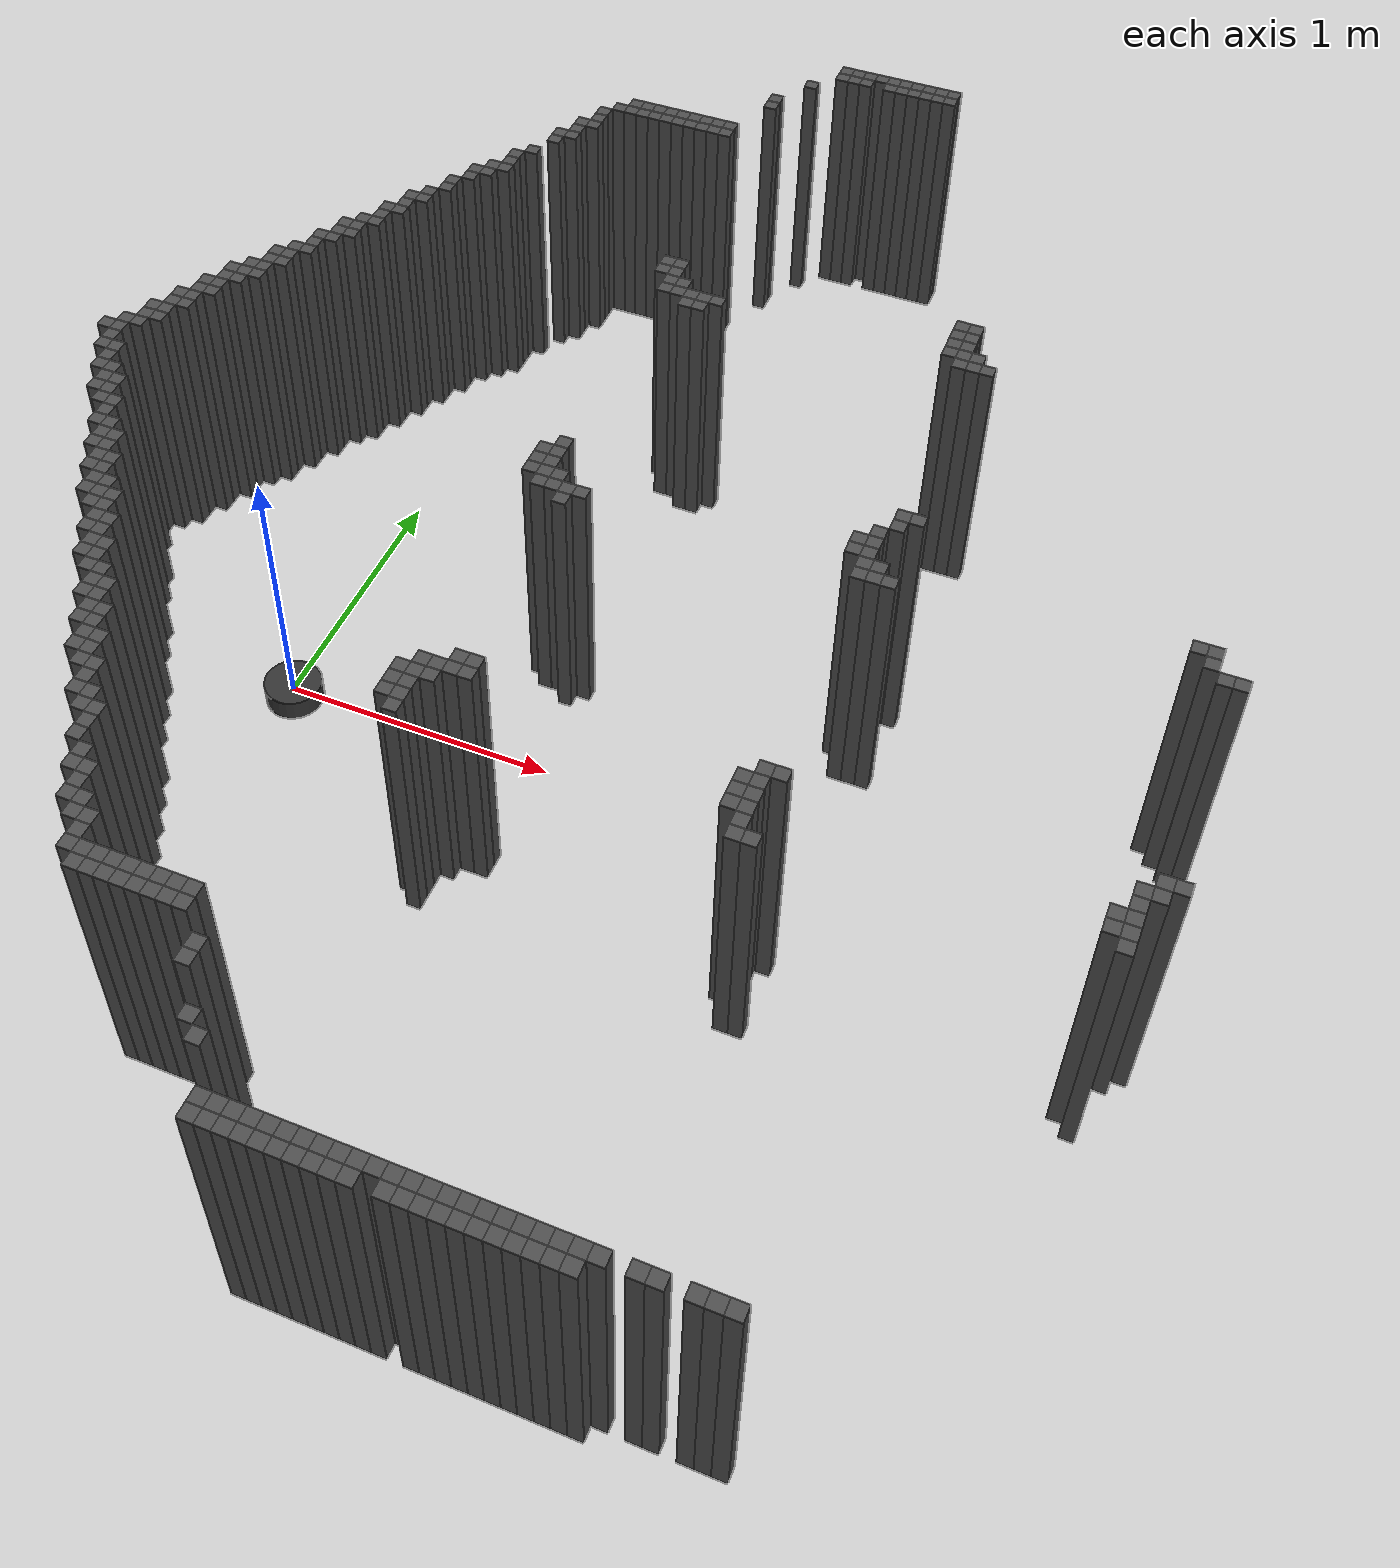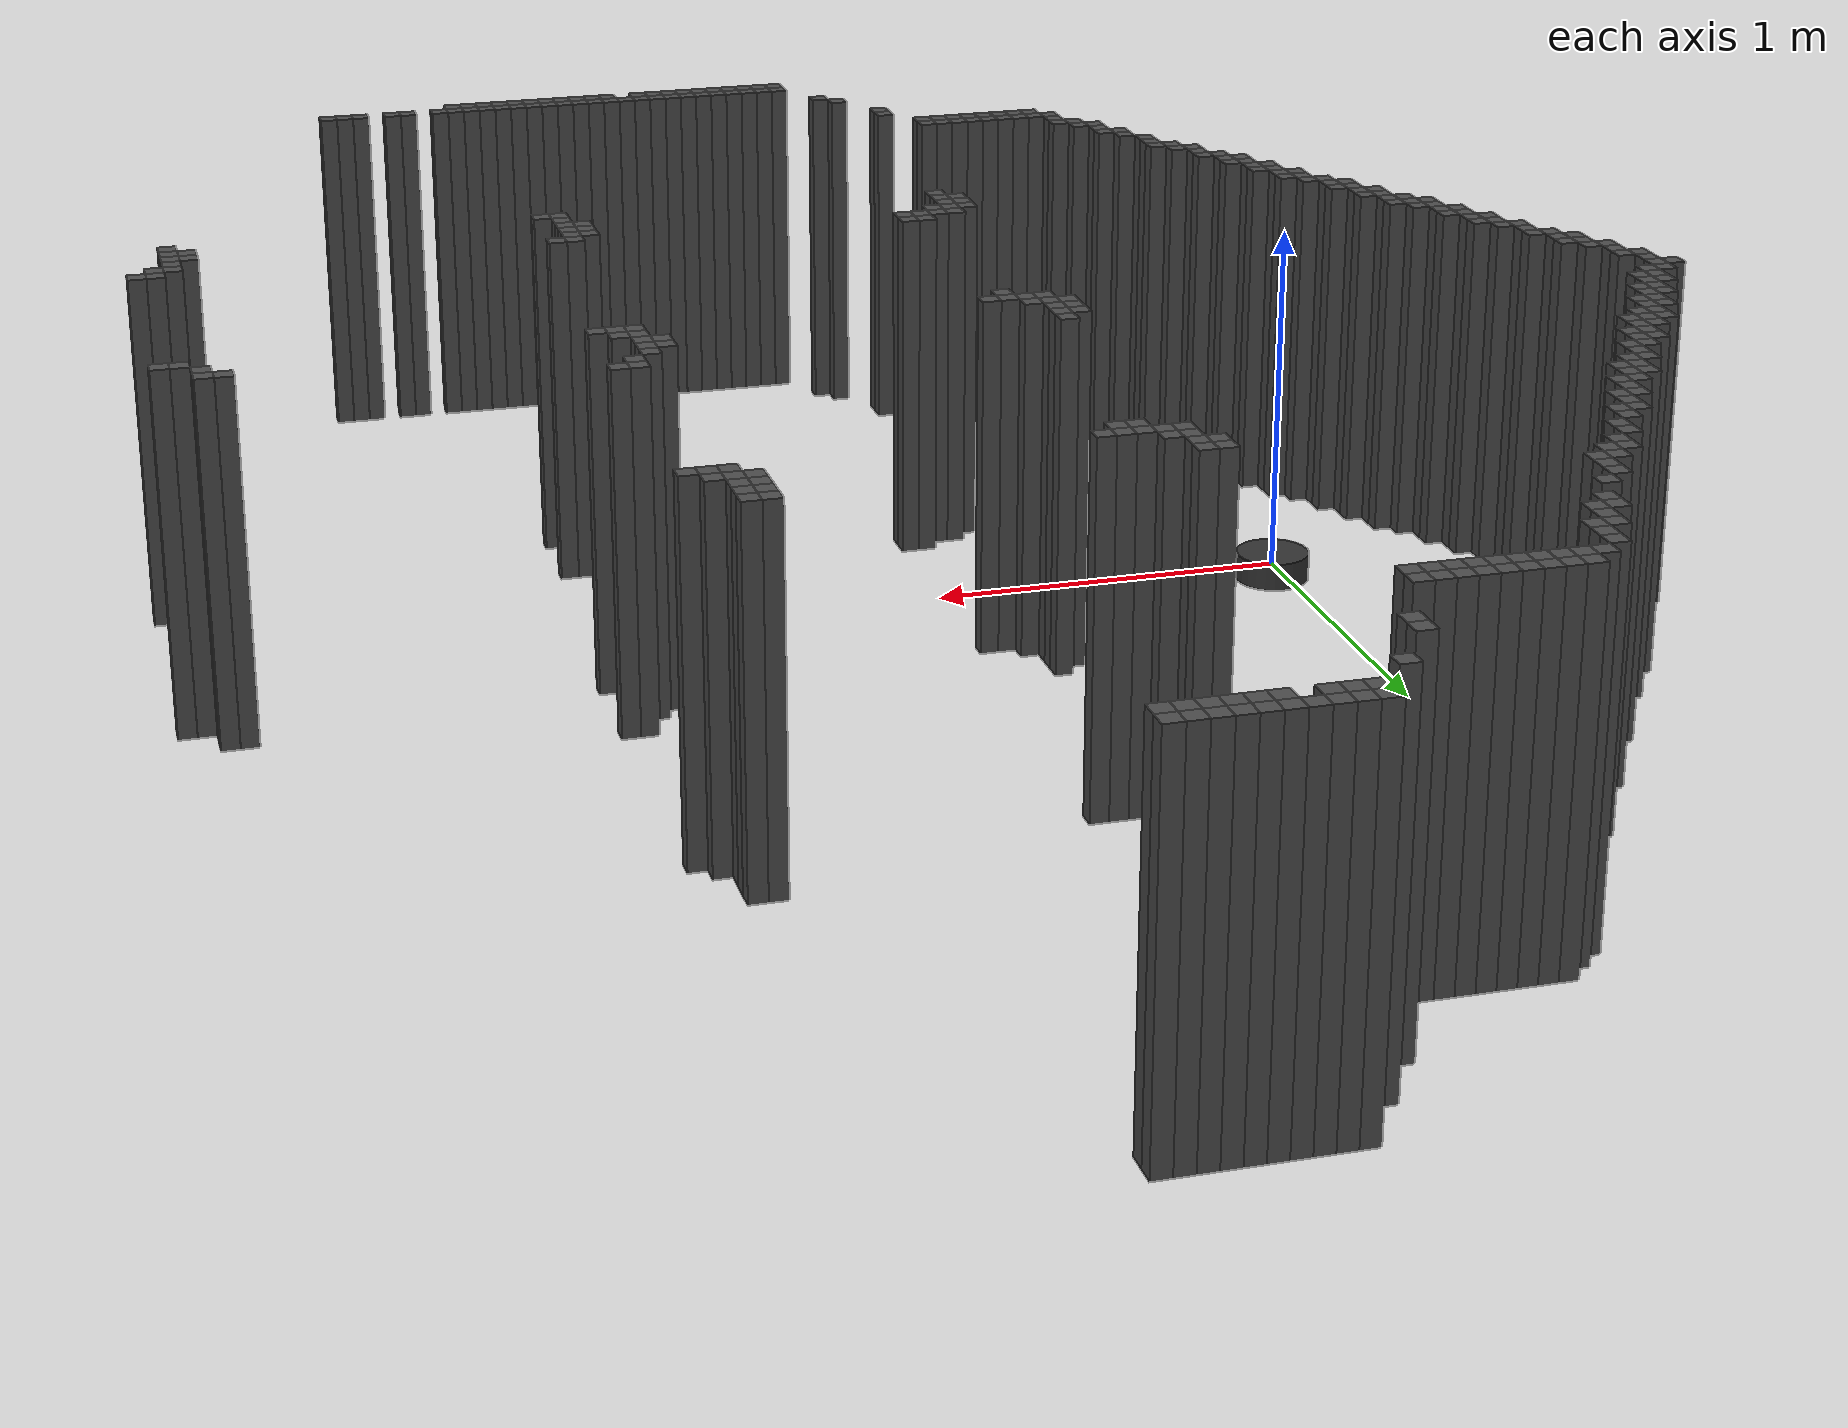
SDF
<sdf version="1.9">
 <world name="house_cleaner">
  <gravity>0 0 -9.81</gravity>
  <model name="wall_5_43">
   <static>true</static>
   <pose>0.9800 3.0900 0.5 0 0 0</pose>
   <link name="wall_link">
    <collision name="collision"><geometry><box><size>0.05 0.05 1.0</size></box></geometry></collision>
    <visual name="visual">
     <geometry><box><size>0.05 0.05 1.0</size></box></geometry>
     <material><ambient>0.3 0.3 0.3 1</ambient><diffuse>0.3 0.3 0.3 1</diffuse></material>
    </visual>
   </link>
  </model>
  <model name="wall_5_44">
   <static>true</static>
   <pose>1.0300 3.0900 0.5 0 0 0</pose>
   <link name="wall_link">
    <collision name="collision"><geometry><box><size>0.05 0.05 1.0</size></box></geometry></collision>
    <visual name="visual">
     <geometry><box><size>0.05 0.05 1.0</size></box></geometry>
     <material><ambient>0.3 0.3 0.3 1</ambient><diffuse>0.3 0.3 0.3 1</diffuse></material>
    </visual>
   </link>
  </model>
  <model name="wall_5_45">
   <static>true</static>
   <pose>1.0800 3.0900 0.5 0 0 0</pose>
   <link name="wall_link">
    <collision name="collision"><geometry><box><size>0.05 0.05 1.0</size></box></geometry></collision>
    <visual name="visual">
     <geometry><box><size>0.05 0.05 1.0</size></box></geometry>
     <material><ambient>0.3 0.3 0.3 1</ambient><diffuse>0.3 0.3 0.3 1</diffuse></material>
    </visual>
   </link>
  </model>
  <model name="wall_5_46">
   <static>true</static>
   <pose>1.1300 3.0900 0.5 0 0 0</pose>
   <link name="wall_link">
    <collision name="collision"><geometry><box><size>0.05 0.05 1.0</size></box></geometry></collision>
    <visual name="visual">
     <geometry><box><size>0.05 0.05 1.0</size></box></geometry>
     <material><ambient>0.3 0.3 0.3 1</ambient><diffuse>0.3 0.3 0.3 1</diffuse></material>
    </visual>
   </link>
  </model>
  <model name="wall_5_47">
   <static>true</static>
   <pose>1.1800 3.0900 0.5 0 0 0</pose>
   <link name="wall_link">
    <collision name="collision"><geometry><box><size>0.05 0.05 1.0</size></box></geometry></collision>
    <visual name="visual">
     <geometry><box><size>0.05 0.05 1.0</size></box></geometry>
     <material><ambient>0.3 0.3 0.3 1</ambient><diffuse>0.3 0.3 0.3 1</diffuse></material>
    </visual>
   </link>
  </model>
  <model name="wall_5_48">
   <static>true</static>
   <pose>1.2300 3.0900 0.5 0 0 0</pose>
   <link name="wall_link">
    <collision name="collision"><geometry><box><size>0.05 0.05 1.0</size></box></geometry></collision>
    <visual name="visual">
     <geometry><box><size>0.05 0.05 1.0</size></box></geometry>
     <material><ambient>0.3 0.3 0.3 1</ambient><diffuse>0.3 0.3 0.3 1</diffuse></material>
    </visual>
   </link>
  </model>
  <model name="wall_5_49">
   <static>true</static>
   <pose>1.2800 3.0900 0.5 0 0 0</pose>
   <link name="wall_link">
    <collision name="collision"><geometry><box><size>0.05 0.05 1.0</size></box></geometry></collision>
    <visual name="visual">
     <geometry><box><size>0.05 0.05 1.0</size></box></geometry>
     <material><ambient>0.3 0.3 0.3 1</ambient><diffuse>0.3 0.3 0.3 1</diffuse></material>
    </visual>
   </link>
  </model>
  <model name="wall_5_50">
   <static>true</static>
   <pose>1.3300 3.0900 0.5 0 0 0</pose>
   <link name="wall_link">
    <collision name="collision"><geometry><box><size>0.05 0.05 1.0</size></box></geometry></collision>
    <visual name="visual">
     <geometry><box><size>0.05 0.05 1.0</size></box></geometry>
     <material><ambient>0.3 0.3 0.3 1</ambient><diffuse>0.3 0.3 0.3 1</diffuse></material>
    </visual>
   </link>
  </model>
  <model name="wall_5_51">
   <static>true</static>
   <pose>1.3800 3.0900 0.5 0 0 0</pose>
   <link name="wall_link">
    <collision name="collision"><geometry><box><size>0.05 0.05 1.0</size></box></geometry></collision>
    <visual name="visual">
     <geometry><box><size>0.05 0.05 1.0</size></box></geometry>
     <material><ambient>0.3 0.3 0.3 1</ambient><diffuse>0.3 0.3 0.3 1</diffuse></material>
    </visual>
   </link>
  </model>
  <model name="wall_5_52">
   <static>true</static>
   <pose>1.4300 3.0900 0.5 0 0 0</pose>
   <link name="wall_link">
    <collision name="collision"><geometry><box><size>0.05 0.05 1.0</size></box></geometry></collision>
    <visual name="visual">
     <geometry><box><size>0.05 0.05 1.0</size></box></geometry>
     <material><ambient>0.3 0.3 0.3 1</ambient><diffuse>0.3 0.3 0.3 1</diffuse></material>
    </visual>
   </link>
  </model>
  <model name="wall_6_43">
   <static>true</static>
   <pose>0.9800 3.0400 0.5 0 0 0</pose>
   <link name="wall_link">
    <collision name="collision"><geometry><box><size>0.05 0.05 1.0</size></box></geometry></collision>
    <visual name="visual">
     <geometry><box><size>0.05 0.05 1.0</size></box></geometry>
     <material><ambient>0.3 0.3 0.3 1</ambient><diffuse>0.3 0.3 0.3 1</diffuse></material>
    </visual>
   </link>
  </model>
  <model name="wall_6_44">
   <static>true</static>
   <pose>1.0300 3.0400 0.5 0 0 0</pose>
   <link name="wall_link">
    <collision name="collision"><geometry><box><size>0.05 0.05 1.0</size></box></geometry></collision>
    <visual name="visual">
     <geometry><box><size>0.05 0.05 1.0</size></box></geometry>
     <material><ambient>0.3 0.3 0.3 1</ambient><diffuse>0.3 0.3 0.3 1</diffuse></material>
    </visual>
   </link>
  </model>
  <model name="wall_6_45">
   <static>true</static>
   <pose>1.0800 3.0400 0.5 0 0 0</pose>
   <link name="wall_link">
    <collision name="collision"><geometry><box><size>0.05 0.05 1.0</size></box></geometry></collision>
    <visual name="visual">
     <geometry><box><size>0.05 0.05 1.0</size></box></geometry>
     <material><ambient>0.3 0.3 0.3 1</ambient><diffuse>0.3 0.3 0.3 1</diffuse></material>
    </visual>
   </link>
  </model>
  <model name="wall_6_47">
   <static>true</static>
   <pose>1.1800 3.0400 0.5 0 0 0</pose>
   <link name="wall_link">
    <collision name="collision"><geometry><box><size>0.05 0.05 1.0</size></box></geometry></collision>
    <visual name="visual">
     <geometry><box><size>0.05 0.05 1.0</size></box></geometry>
     <material><ambient>0.3 0.3 0.3 1</ambient><diffuse>0.3 0.3 0.3 1</diffuse></material>
    </visual>
   </link>
  </model>
  <model name="wall_6_48">
   <static>true</static>
   <pose>1.2300 3.0400 0.5 0 0 0</pose>
   <link name="wall_link">
    <collision name="collision"><geometry><box><size>0.05 0.05 1.0</size></box></geometry></collision>
    <visual name="visual">
     <geometry><box><size>0.05 0.05 1.0</size></box></geometry>
     <material><ambient>0.3 0.3 0.3 1</ambient><diffuse>0.3 0.3 0.3 1</diffuse></material>
    </visual>
   </link>
  </model>
  <model name="wall_6_49">
   <static>true</static>
   <pose>1.2800 3.0400 0.5 0 0 0</pose>
   <link name="wall_link">
    <collision name="collision"><geometry><box><size>0.05 0.05 1.0</size></box></geometry></collision>
    <visual name="visual">
     <geometry><box><size>0.05 0.05 1.0</size></box></geometry>
     <material><ambient>0.3 0.3 0.3 1</ambient><diffuse>0.3 0.3 0.3 1</diffuse></material>
    </visual>
   </link>
  </model>
  <model name="wall_6_50">
   <static>true</static>
   <pose>1.3300 3.0400 0.5 0 0 0</pose>
   <link name="wall_link">
    <collision name="collision"><geometry><box><size>0.05 0.05 1.0</size></box></geometry></collision>
    <visual name="visual">
     <geometry><box><size>0.05 0.05 1.0</size></box></geometry>
     <material><ambient>0.3 0.3 0.3 1</ambient><diffuse>0.3 0.3 0.3 1</diffuse></material>
    </visual>
   </link>
  </model>
  <model name="wall_6_51">
   <static>true</static>
   <pose>1.3800 3.0400 0.5 0 0 0</pose>
   <link name="wall_link">
    <collision name="collision"><geometry><box><size>0.05 0.05 1.0</size></box></geometry></collision>
    <visual name="visual">
     <geometry><box><size>0.05 0.05 1.0</size></box></geometry>
     <material><ambient>0.3 0.3 0.3 1</ambient><diffuse>0.3 0.3 0.3 1</diffuse></material>
    </visual>
   </link>
  </model>
  <model name="wall_6_52">
   <static>true</static>
   <pose>1.4300 3.0400 0.5 0 0 0</pose>
   <link name="wall_link">
    <collision name="collision"><geometry><box><size>0.05 0.05 1.0</size></box></geometry></collision>
    <visual name="visual">
     <geometry><box><size>0.05 0.05 1.0</size></box></geometry>
     <material><ambient>0.3 0.3 0.3 1</ambient><diffuse>0.3 0.3 0.3 1</diffuse></material>
    </visual>
   </link>
  </model>
  <model name="wall_8_41">
   <static>true</static>
   <pose>0.8800 2.9400 0.5 0 0 0</pose>
   <link name="wall_link">
    <collision name="collision"><geometry><box><size>0.05 0.05 1.0</size></box></geometry></collision>
    <visual name="visual">
     <geometry><box><size>0.05 0.05 1.0</size></box></geometry>
     <material><ambient>0.3 0.3 0.3 1</ambient><diffuse>0.3 0.3 0.3 1</diffuse></material>
    </visual>
   </link>
  </model>
  <model name="wall_11_39">
   <static>true</static>
   <pose>0.7800 2.7900 0.5 0 0 0</pose>
   <link name="wall_link">
    <collision name="collision"><geometry><box><size>0.05 0.05 1.0</size></box></geometry></collision>
    <visual name="visual">
     <geometry><box><size>0.05 0.05 1.0</size></box></geometry>
     <material><ambient>0.3 0.3 0.3 1</ambient><diffuse>0.3 0.3 0.3 1</diffuse></material>
    </visual>
   </link>
  </model>
  <model name="wall_12_39">
   <static>true</static>
   <pose>0.7800 2.7400 0.5 0 0 0</pose>
   <link name="wall_link">
    <collision name="collision"><geometry><box><size>0.05 0.05 1.0</size></box></geometry></collision>
    <visual name="visual">
     <geometry><box><size>0.05 0.05 1.0</size></box></geometry>
     <material><ambient>0.3 0.3 0.3 1</ambient><diffuse>0.3 0.3 0.3 1</diffuse></material>
    </visual>
   </link>
  </model>
  <model name="wall_16_29">
   <static>true</static>
   <pose>0.2800 2.5400 0.5 0 0 0</pose>
   <link name="wall_link">
    <collision name="collision"><geometry><box><size>0.05 0.05 1.0</size></box></geometry></collision>
    <visual name="visual">
     <geometry><box><size>0.05 0.05 1.0</size></box></geometry>
     <material><ambient>0.3 0.3 0.3 1</ambient><diffuse>0.3 0.3 0.3 1</diffuse></material>
    </visual>
   </link>
  </model>
  <model name="wall_16_30">
   <static>true</static>
   <pose>0.3300 2.5400 0.5 0 0 0</pose>
   <link name="wall_link">
    <collision name="collision"><geometry><box><size>0.05 0.05 1.0</size></box></geometry></collision>
    <visual name="visual">
     <geometry><box><size>0.05 0.05 1.0</size></box></geometry>
     <material><ambient>0.3 0.3 0.3 1</ambient><diffuse>0.3 0.3 0.3 1</diffuse></material>
    </visual>
   </link>
  </model>
  <model name="wall_16_31">
   <static>true</static>
   <pose>0.3800 2.5400 0.5 0 0 0</pose>
   <link name="wall_link">
    <collision name="collision"><geometry><box><size>0.05 0.05 1.0</size></box></geometry></collision>
    <visual name="visual">
     <geometry><box><size>0.05 0.05 1.0</size></box></geometry>
     <material><ambient>0.3 0.3 0.3 1</ambient><diffuse>0.3 0.3 0.3 1</diffuse></material>
    </visual>
   </link>
  </model>
  <model name="wall_16_32">
   <static>true</static>
   <pose>0.4300 2.5400 0.5 0 0 0</pose>
   <link name="wall_link">
    <collision name="collision"><geometry><box><size>0.05 0.05 1.0</size></box></geometry></collision>
    <visual name="visual">
     <geometry><box><size>0.05 0.05 1.0</size></box></geometry>
     <material><ambient>0.3 0.3 0.3 1</ambient><diffuse>0.3 0.3 0.3 1</diffuse></material>
    </visual>
   </link>
  </model>
  <model name="wall_16_33">
   <static>true</static>
   <pose>0.4800 2.5400 0.5 0 0 0</pose>
   <link name="wall_link">
    <collision name="collision"><geometry><box><size>0.05 0.05 1.0</size></box></geometry></collision>
    <visual name="visual">
     <geometry><box><size>0.05 0.05 1.0</size></box></geometry>
     <material><ambient>0.3 0.3 0.3 1</ambient><diffuse>0.3 0.3 0.3 1</diffuse></material>
    </visual>
   </link>
  </model>
  <model name="wall_16_34">
   <static>true</static>
   <pose>0.5300 2.5400 0.5 0 0 0</pose>
   <link name="wall_link">
    <collision name="collision"><geometry><box><size>0.05 0.05 1.0</size></box></geometry></collision>
    <visual name="visual">
     <geometry><box><size>0.05 0.05 1.0</size></box></geometry>
     <material><ambient>0.3 0.3 0.3 1</ambient><diffuse>0.3 0.3 0.3 1</diffuse></material>
    </visual>
   </link>
  </model>
  <model name="wall_16_35">
   <static>true</static>
   <pose>0.5800 2.5400 0.5 0 0 0</pose>
   <link name="wall_link">
    <collision name="collision"><geometry><box><size>0.05 0.05 1.0</size></box></geometry></collision>
    <visual name="visual">
     <geometry><box><size>0.05 0.05 1.0</size></box></geometry>
     <material><ambient>0.3 0.3 0.3 1</ambient><diffuse>0.3 0.3 0.3 1</diffuse></material>
    </visual>
   </link>
  </model>
  <model name="wall_16_36">
   <static>true</static>
   <pose>0.6300 2.5400 0.5 0 0 0</pose>
   <link name="wall_link">
    <collision name="collision"><geometry><box><size>0.05 0.05 1.0</size></box></geometry></collision>
    <visual name="visual">
     <geometry><box><size>0.05 0.05 1.0</size></box></geometry>
     <material><ambient>0.3 0.3 0.3 1</ambient><diffuse>0.3 0.3 0.3 1</diffuse></material>
    </visual>
   </link>
  </model>
  <model name="wall_16_37">
   <static>true</static>
   <pose>0.6800 2.5400 0.5 0 0 0</pose>
   <link name="wall_link">
    <collision name="collision"><geometry><box><size>0.05 0.05 1.0</size></box></geometry></collision>
    <visual name="visual">
     <geometry><box><size>0.05 0.05 1.0</size></box></geometry>
     <material><ambient>0.3 0.3 0.3 1</ambient><diffuse>0.3 0.3 0.3 1</diffuse></material>
    </visual>
   </link>
  </model>
  <model name="wall_17_28">
   <static>true</static>
   <pose>0.2300 2.4900 0.5 0 0 0</pose>
   <link name="wall_link">
    <collision name="collision"><geometry><box><size>0.05 0.05 1.0</size></box></geometry></collision>
    <visual name="visual">
     <geometry><box><size>0.05 0.05 1.0</size></box></geometry>
     <material><ambient>0.3 0.3 0.3 1</ambient><diffuse>0.3 0.3 0.3 1</diffuse></material>
    </visual>
   </link>
  </model>
  <model name="wall_17_29">
   <static>true</static>
   <pose>0.2800 2.4900 0.5 0 0 0</pose>
   <link name="wall_link">
    <collision name="collision"><geometry><box><size>0.05 0.05 1.0</size></box></geometry></collision>
    <visual name="visual">
     <geometry><box><size>0.05 0.05 1.0</size></box></geometry>
     <material><ambient>0.3 0.3 0.3 1</ambient><diffuse>0.3 0.3 0.3 1</diffuse></material>
    </visual>
   </link>
  </model>
  <model name="wall_17_30">
   <static>true</static>
   <pose>0.3300 2.4900 0.5 0 0 0</pose>
   <link name="wall_link">
    <collision name="collision"><geometry><box><size>0.05 0.05 1.0</size></box></geometry></collision>
    <visual name="visual">
     <geometry><box><size>0.05 0.05 1.0</size></box></geometry>
     <material><ambient>0.3 0.3 0.3 1</ambient><diffuse>0.3 0.3 0.3 1</diffuse></material>
    </visual>
   </link>
  </model>
  <model name="wall_17_31">
   <static>true</static>
   <pose>0.3800 2.4900 0.5 0 0 0</pose>
   <link name="wall_link">
    <collision name="collision"><geometry><box><size>0.05 0.05 1.0</size></box></geometry></collision>
    <visual name="visual">
     <geometry><box><size>0.05 0.05 1.0</size></box></geometry>
     <material><ambient>0.3 0.3 0.3 1</ambient><diffuse>0.3 0.3 0.3 1</diffuse></material>
    </visual>
   </link>
  </model>
  <model name="wall_17_32">
   <static>true</static>
   <pose>0.4300 2.4900 0.5 0 0 0</pose>
   <link name="wall_link">
    <collision name="collision"><geometry><box><size>0.05 0.05 1.0</size></box></geometry></collision>
    <visual name="visual">
     <geometry><box><size>0.05 0.05 1.0</size></box></geometry>
     <material><ambient>0.3 0.3 0.3 1</ambient><diffuse>0.3 0.3 0.3 1</diffuse></material>
    </visual>
   </link>
  </model>
  <model name="wall_17_33">
   <static>true</static>
   <pose>0.4800 2.4900 0.5 0 0 0</pose>
   <link name="wall_link">
    <collision name="collision"><geometry><box><size>0.05 0.05 1.0</size></box></geometry></collision>
    <visual name="visual">
     <geometry><box><size>0.05 0.05 1.0</size></box></geometry>
     <material><ambient>0.3 0.3 0.3 1</ambient><diffuse>0.3 0.3 0.3 1</diffuse></material>
    </visual>
   </link>
  </model>
  <model name="wall_17_34">
   <static>true</static>
   <pose>0.5300 2.4900 0.5 0 0 0</pose>
   <link name="wall_link">
    <collision name="collision"><geometry><box><size>0.05 0.05 1.0</size></box></geometry></collision>
    <visual name="visual">
     <geometry><box><size>0.05 0.05 1.0</size></box></geometry>
     <material><ambient>0.3 0.3 0.3 1</ambient><diffuse>0.3 0.3 0.3 1</diffuse></material>
    </visual>
   </link>
  </model>
  <model name="wall_17_35">
   <static>true</static>
   <pose>0.5800 2.4900 0.5 0 0 0</pose>
   <link name="wall_link">
    <collision name="collision"><geometry><box><size>0.05 0.05 1.0</size></box></geometry></collision>
    <visual name="visual">
     <geometry><box><size>0.05 0.05 1.0</size></box></geometry>
     <material><ambient>0.3 0.3 0.3 1</ambient><diffuse>0.3 0.3 0.3 1</diffuse></material>
    </visual>
   </link>
  </model>
  <model name="wall_17_36">
   <static>true</static>
   <pose>0.6300 2.4900 0.5 0 0 0</pose>
   <link name="wall_link">
    <collision name="collision"><geometry><box><size>0.05 0.05 1.0</size></box></geometry></collision>
    <visual name="visual">
     <geometry><box><size>0.05 0.05 1.0</size></box></geometry>
     <material><ambient>0.3 0.3 0.3 1</ambient><diffuse>0.3 0.3 0.3 1</diffuse></material>
    </visual>
   </link>
  </model>
  <model name="wall_17_37">
   <static>true</static>
   <pose>0.6800 2.4900 0.5 0 0 0</pose>
   <link name="wall_link">
    <collision name="collision"><geometry><box><size>0.05 0.05 1.0</size></box></geometry></collision>
    <visual name="visual">
     <geometry><box><size>0.05 0.05 1.0</size></box></geometry>
     <material><ambient>0.3 0.3 0.3 1</ambient><diffuse>0.3 0.3 0.3 1</diffuse></material>
    </visual>
   </link>
  </model>
  <model name="wall_18_27">
   <static>true</static>
   <pose>0.1800 2.4400 0.5 0 0 0</pose>
   <link name="wall_link">
    <collision name="collision"><geometry><box><size>0.05 0.05 1.0</size></box></geometry></collision>
    <visual name="visual">
     <geometry><box><size>0.05 0.05 1.0</size></box></geometry>
     <material><ambient>0.3 0.3 0.3 1</ambient><diffuse>0.3 0.3 0.3 1</diffuse></material>
    </visual>
   </link>
  </model>
  <model name="wall_19_27">
   <static>true</static>
   <pose>0.1800 2.3900 0.5 0 0 0</pose>
   <link name="wall_link">
    <collision name="collision"><geometry><box><size>0.05 0.05 1.0</size></box></geometry></collision>
    <visual name="visual">
     <geometry><box><size>0.05 0.05 1.0</size></box></geometry>
     <material><ambient>0.3 0.3 0.3 1</ambient><diffuse>0.3 0.3 0.3 1</diffuse></material>
    </visual>
   </link>
  </model>
  <model name="wall_20_26">
   <static>true</static>
   <pose>0.1300 2.3400 0.5 0 0 0</pose>
   <link name="wall_link">
    <collision name="collision"><geometry><box><size>0.05 0.05 1.0</size></box></geometry></collision>
    <visual name="visual">
     <geometry><box><size>0.05 0.05 1.0</size></box></geometry>
     <material><ambient>0.3 0.3 0.3 1</ambient><diffuse>0.3 0.3 0.3 1</diffuse></material>
    </visual>
   </link>
  </model>
  <model name="wall_20_27">
   <static>true</static>
   <pose>0.1800 2.3400 0.5 0 0 0</pose>
   <link name="wall_link">
    <collision name="collision"><geometry><box><size>0.05 0.05 1.0</size></box></geometry></collision>
    <visual name="visual">
     <geometry><box><size>0.05 0.05 1.0</size></box></geometry>
     <material><ambient>0.3 0.3 0.3 1</ambient><diffuse>0.3 0.3 0.3 1</diffuse></material>
    </visual>
   </link>
  </model>
  <model name="wall_21_26">
   <static>true</static>
   <pose>0.1300 2.2900 0.5 0 0 0</pose>
   <link name="wall_link">
    <collision name="collision"><geometry><box><size>0.05 0.05 1.0</size></box></geometry></collision>
    <visual name="visual">
     <geometry><box><size>0.05 0.05 1.0</size></box></geometry>
     <material><ambient>0.3 0.3 0.3 1</ambient><diffuse>0.3 0.3 0.3 1</diffuse></material>
    </visual>
   </link>
  </model>
  <model name="wall_22_25">
   <static>true</static>
   <pose>0.0800 2.2400 0.5 0 0 0</pose>
   <link name="wall_link">
    <collision name="collision"><geometry><box><size>0.05 0.05 1.0</size></box></geometry></collision>
    <visual name="visual">
     <geometry><box><size>0.05 0.05 1.0</size></box></geometry>
     <material><ambient>0.3 0.3 0.3 1</ambient><diffuse>0.3 0.3 0.3 1</diffuse></material>
    </visual>
   </link>
  </model>
  <model name="wall_22_26">
   <static>true</static>
   <pose>0.1300 2.2400 0.5 0 0 0</pose>
   <link name="wall_link">
    <collision name="collision"><geometry><box><size>0.05 0.05 1.0</size></box></geometry></collision>
    <visual name="visual">
     <geometry><box><size>0.05 0.05 1.0</size></box></geometry>
     <material><ambient>0.3 0.3 0.3 1</ambient><diffuse>0.3 0.3 0.3 1</diffuse></material>
    </visual>
   </link>
  </model>
  <model name="wall_23_25">
   <static>true</static>
   <pose>0.0800 2.1900 0.5 0 0 0</pose>
   <link name="wall_link">
    <collision name="collision"><geometry><box><size>0.05 0.05 1.0</size></box></geometry></collision>
    <visual name="visual">
     <geometry><box><size>0.05 0.05 1.0</size></box></geometry>
     <material><ambient>0.3 0.3 0.3 1</ambient><diffuse>0.3 0.3 0.3 1</diffuse></material>
    </visual>
   </link>
  </model>
  <model name="wall_25_24">
   <static>true</static>
   <pose>0.0300 2.0900 0.5 0 0 0</pose>
   <link name="wall_link">
    <collision name="collision"><geometry><box><size>0.05 0.05 1.0</size></box></geometry></collision>
    <visual name="visual">
     <geometry><box><size>0.05 0.05 1.0</size></box></geometry>
     <material><ambient>0.3 0.3 0.3 1</ambient><diffuse>0.3 0.3 0.3 1</diffuse></material>
    </visual>
   </link>
  </model>
  <model name="wall_26_23">
   <static>true</static>
   <pose>-0.0200 2.0400 0.5 0 0 0</pose>
   <link name="wall_link">
    <collision name="collision"><geometry><box><size>0.05 0.05 1.0</size></box></geometry></collision>
    <visual name="visual">
     <geometry><box><size>0.05 0.05 1.0</size></box></geometry>
     <material><ambient>0.3 0.3 0.3 1</ambient><diffuse>0.3 0.3 0.3 1</diffuse></material>
    </visual>
   </link>
  </model>
  <model name="wall_27_23">
   <static>true</static>
   <pose>-0.0200 1.9900 0.5 0 0 0</pose>
   <link name="wall_link">
    <collision name="collision"><geometry><box><size>0.05 0.05 1.0</size></box></geometry></collision>
    <visual name="visual">
     <geometry><box><size>0.05 0.05 1.0</size></box></geometry>
     <material><ambient>0.3 0.3 0.3 1</ambient><diffuse>0.3 0.3 0.3 1</diffuse></material>
    </visual>
   </link>
  </model>
  <model name="wall_28_22">
   <static>true</static>
   <pose>-0.0700 1.9400 0.5 0 0 0</pose>
   <link name="wall_link">
    <collision name="collision"><geometry><box><size>0.05 0.05 1.0</size></box></geometry></collision>
    <visual name="visual">
     <geometry><box><size>0.05 0.05 1.0</size></box></geometry>
     <material><ambient>0.3 0.3 0.3 1</ambient><diffuse>0.3 0.3 0.3 1</diffuse></material>
    </visual>
   </link>
  </model>
  <model name="wall_28_23">
   <static>true</static>
   <pose>-0.0200 1.9400 0.5 0 0 0</pose>
   <link name="wall_link">
    <collision name="collision"><geometry><box><size>0.05 0.05 1.0</size></box></geometry></collision>
    <visual name="visual">
     <geometry><box><size>0.05 0.05 1.0</size></box></geometry>
     <material><ambient>0.3 0.3 0.3 1</ambient><diffuse>0.3 0.3 0.3 1</diffuse></material>
    </visual>
   </link>
  </model>
  <model name="wall_29_21">
   <static>true</static>
   <pose>-0.1200 1.8900 0.5 0 0 0</pose>
   <link name="wall_link">
    <collision name="collision"><geometry><box><size>0.05 0.05 1.0</size></box></geometry></collision>
    <visual name="visual">
     <geometry><box><size>0.05 0.05 1.0</size></box></geometry>
     <material><ambient>0.3 0.3 0.3 1</ambient><diffuse>0.3 0.3 0.3 1</diffuse></material>
    </visual>
   </link>
  </model>
  <model name="wall_29_22">
   <static>true</static>
   <pose>-0.0700 1.8900 0.5 0 0 0</pose>
   <link name="wall_link">
    <collision name="collision"><geometry><box><size>0.05 0.05 1.0</size></box></geometry></collision>
    <visual name="visual">
     <geometry><box><size>0.05 0.05 1.0</size></box></geometry>
     <material><ambient>0.3 0.3 0.3 1</ambient><diffuse>0.3 0.3 0.3 1</diffuse></material>
    </visual>
   </link>
  </model>
  <model name="wall_30_21">
   <static>true</static>
   <pose>-0.1200 1.8400 0.5 0 0 0</pose>
   <link name="wall_link">
    <collision name="collision"><geometry><box><size>0.05 0.05 1.0</size></box></geometry></collision>
    <visual name="visual">
     <geometry><box><size>0.05 0.05 1.0</size></box></geometry>
     <material><ambient>0.3 0.3 0.3 1</ambient><diffuse>0.3 0.3 0.3 1</diffuse></material>
    </visual>
   </link>
  </model>
  <model name="wall_31_20">
   <static>true</static>
   <pose>-0.1700 1.7900 0.5 0 0 0</pose>
   <link name="wall_link">
    <collision name="collision"><geometry><box><size>0.05 0.05 1.0</size></box></geometry></collision>
    <visual name="visual">
     <geometry><box><size>0.05 0.05 1.0</size></box></geometry>
     <material><ambient>0.3 0.3 0.3 1</ambient><diffuse>0.3 0.3 0.3 1</diffuse></material>
    </visual>
   </link>
  </model>
  <model name="wall_32_20">
   <static>true</static>
   <pose>-0.1700 1.7400 0.5 0 0 0</pose>
   <link name="wall_link">
    <collision name="collision"><geometry><box><size>0.05 0.05 1.0</size></box></geometry></collision>
    <visual name="visual">
     <geometry><box><size>0.05 0.05 1.0</size></box></geometry>
     <material><ambient>0.3 0.3 0.3 1</ambient><diffuse>0.3 0.3 0.3 1</diffuse></material>
    </visual>
   </link>
  </model>
  <model name="wall_33_19">
   <static>true</static>
   <pose>-0.2200 1.6900 0.5 0 0 0</pose>
   <link name="wall_link">
    <collision name="collision"><geometry><box><size>0.05 0.05 1.0</size></box></geometry></collision>
    <visual name="visual">
     <geometry><box><size>0.05 0.05 1.0</size></box></geometry>
     <material><ambient>0.3 0.3 0.3 1</ambient><diffuse>0.3 0.3 0.3 1</diffuse></material>
    </visual>
   </link>
  </model>
  <model name="wall_33_61">
   <static>true</static>
   <pose>1.8800 1.6900 0.5 0 0 0</pose>
   <link name="wall_link">
    <collision name="collision"><geometry><box><size>0.05 0.05 1.0</size></box></geometry></collision>
    <visual name="visual">
     <geometry><box><size>0.05 0.05 1.0</size></box></geometry>
     <material><ambient>0.3 0.3 0.3 1</ambient><diffuse>0.3 0.3 0.3 1</diffuse></material>
    </visual>
   </link>
  </model>
  <model name="wall_33_62">
   <static>true</static>
   <pose>1.9300 1.6900 0.5 0 0 0</pose>
   <link name="wall_link">
    <collision name="collision"><geometry><box><size>0.05 0.05 1.0</size></box></geometry></collision>
    <visual name="visual">
     <geometry><box><size>0.05 0.05 1.0</size></box></geometry>
     <material><ambient>0.3 0.3 0.3 1</ambient><diffuse>0.3 0.3 0.3 1</diffuse></material>
    </visual>
   </link>
  </model>
  <model name="wall_34_18">
   <static>true</static>
   <pose>-0.2700 1.6400 0.5 0 0 0</pose>
   <link name="wall_link">
    <collision name="collision"><geometry><box><size>0.05 0.05 1.0</size></box></geometry></collision>
    <visual name="visual">
     <geometry><box><size>0.05 0.05 1.0</size></box></geometry>
     <material><ambient>0.3 0.3 0.3 1</ambient><diffuse>0.3 0.3 0.3 1</diffuse></material>
    </visual>
   </link>
  </model>
  <model name="wall_34_19">
   <static>true</static>
   <pose>-0.2200 1.6400 0.5 0 0 0</pose>
   <link name="wall_link">
    <collision name="collision"><geometry><box><size>0.05 0.05 1.0</size></box></geometry></collision>
    <visual name="visual">
     <geometry><box><size>0.05 0.05 1.0</size></box></geometry>
     <material><ambient>0.3 0.3 0.3 1</ambient><diffuse>0.3 0.3 0.3 1</diffuse></material>
    </visual>
   </link>
  </model>
  <model name="wall_34_39">
   <static>true</static>
   <pose>0.7800 1.6400 0.5 0 0 0</pose>
   <link name="wall_link">
    <collision name="collision"><geometry><box><size>0.05 0.05 1.0</size></box></geometry></collision>
    <visual name="visual">
     <geometry><box><size>0.05 0.05 1.0</size></box></geometry>
     <material><ambient>0.3 0.3 0.3 1</ambient><diffuse>0.3 0.3 0.3 1</diffuse></material>
    </visual>
   </link>
  </model>
  <model name="wall_34_40">
   <static>true</static>
   <pose>0.8300 1.6400 0.5 0 0 0</pose>
   <link name="wall_link">
    <collision name="collision"><geometry><box><size>0.05 0.05 1.0</size></box></geometry></collision>
    <visual name="visual">
     <geometry><box><size>0.05 0.05 1.0</size></box></geometry>
     <material><ambient>0.3 0.3 0.3 1</ambient><diffuse>0.3 0.3 0.3 1</diffuse></material>
    </visual>
   </link>
  </model>
  <model name="wall_34_61">
   <static>true</static>
   <pose>1.8800 1.6400 0.5 0 0 0</pose>
   <link name="wall_link">
    <collision name="collision"><geometry><box><size>0.05 0.05 1.0</size></box></geometry></collision>
    <visual name="visual">
     <geometry><box><size>0.05 0.05 1.0</size></box></geometry>
     <material><ambient>0.3 0.3 0.3 1</ambient><diffuse>0.3 0.3 0.3 1</diffuse></material>
    </visual>
   </link>
  </model>
  <model name="wall_34_62">
   <static>true</static>
   <pose>1.9300 1.6400 0.5 0 0 0</pose>
   <link name="wall_link">
    <collision name="collision"><geometry><box><size>0.05 0.05 1.0</size></box></geometry></collision>
    <visual name="visual">
     <geometry><box><size>0.05 0.05 1.0</size></box></geometry>
     <material><ambient>0.3 0.3 0.3 1</ambient><diffuse>0.3 0.3 0.3 1</diffuse></material>
    </visual>
   </link>
  </model>
  <model name="wall_35_18">
   <static>true</static>
   <pose>-0.2700 1.5900 0.5 0 0 0</pose>
   <link name="wall_link">
    <collision name="collision"><geometry><box><size>0.05 0.05 1.0</size></box></geometry></collision>
    <visual name="visual">
     <geometry><box><size>0.05 0.05 1.0</size></box></geometry>
     <material><ambient>0.3 0.3 0.3 1</ambient><diffuse>0.3 0.3 0.3 1</diffuse></material>
    </visual>
   </link>
  </model>
  <model name="wall_35_39">
   <static>true</static>
   <pose>0.7800 1.5900 0.5 0 0 0</pose>
   <link name="wall_link">
    <collision name="collision"><geometry><box><size>0.05 0.05 1.0</size></box></geometry></collision>
    <visual name="visual">
     <geometry><box><size>0.05 0.05 1.0</size></box></geometry>
     <material><ambient>0.3 0.3 0.3 1</ambient><diffuse>0.3 0.3 0.3 1</diffuse></material>
    </visual>
   </link>
  </model>
  <model name="wall_35_40">
   <static>true</static>
   <pose>0.8300 1.5900 0.5 0 0 0</pose>
   <link name="wall_link">
    <collision name="collision"><geometry><box><size>0.05 0.05 1.0</size></box></geometry></collision>
    <visual name="visual">
     <geometry><box><size>0.05 0.05 1.0</size></box></geometry>
     <material><ambient>0.3 0.3 0.3 1</ambient><diffuse>0.3 0.3 0.3 1</diffuse></material>
    </visual>
   </link>
  </model>
  <model name="wall_35_61">
   <static>true</static>
   <pose>1.8800 1.5900 0.5 0 0 0</pose>
   <link name="wall_link">
    <collision name="collision"><geometry><box><size>0.05 0.05 1.0</size></box></geometry></collision>
    <visual name="visual">
     <geometry><box><size>0.05 0.05 1.0</size></box></geometry>
     <material><ambient>0.3 0.3 0.3 1</ambient><diffuse>0.3 0.3 0.3 1</diffuse></material>
    </visual>
   </link>
  </model>
  <model name="wall_35_62">
   <static>true</static>
   <pose>1.9300 1.5900 0.5 0 0 0</pose>
   <link name="wall_link">
    <collision name="collision"><geometry><box><size>0.05 0.05 1.0</size></box></geometry></collision>
    <visual name="visual">
     <geometry><box><size>0.05 0.05 1.0</size></box></geometry>
     <material><ambient>0.3 0.3 0.3 1</ambient><diffuse>0.3 0.3 0.3 1</diffuse></material>
    </visual>
   </link>
  </model>
  <model name="wall_36_17">
   <static>true</static>
   <pose>-0.3200 1.5400 0.5 0 0 0</pose>
   <link name="wall_link">
    <collision name="collision"><geometry><box><size>0.05 0.05 1.0</size></box></geometry></collision>
    <visual name="visual">
     <geometry><box><size>0.05 0.05 1.0</size></box></geometry>
     <material><ambient>0.3 0.3 0.3 1</ambient><diffuse>0.3 0.3 0.3 1</diffuse></material>
    </visual>
   </link>
  </model>
  <model name="wall_36_18">
   <static>true</static>
   <pose>-0.2700 1.5400 0.5 0 0 0</pose>
   <link name="wall_link">
    <collision name="collision"><geometry><box><size>0.05 0.05 1.0</size></box></geometry></collision>
    <visual name="visual">
     <geometry><box><size>0.05 0.05 1.0</size></box></geometry>
     <material><ambient>0.3 0.3 0.3 1</ambient><diffuse>0.3 0.3 0.3 1</diffuse></material>
    </visual>
   </link>
  </model>
  <model name="wall_36_40">
   <static>true</static>
   <pose>0.8300 1.5400 0.5 0 0 0</pose>
   <link name="wall_link">
    <collision name="collision"><geometry><box><size>0.05 0.05 1.0</size></box></geometry></collision>
    <visual name="visual">
     <geometry><box><size>0.05 0.05 1.0</size></box></geometry>
     <material><ambient>0.3 0.3 0.3 1</ambient><diffuse>0.3 0.3 0.3 1</diffuse></material>
    </visual>
   </link>
  </model>
  <model name="wall_36_41">
   <static>true</static>
   <pose>0.8800 1.5400 0.5 0 0 0</pose>
   <link name="wall_link">
    <collision name="collision"><geometry><box><size>0.05 0.05 1.0</size></box></geometry></collision>
    <visual name="visual">
     <geometry><box><size>0.05 0.05 1.0</size></box></geometry>
     <material><ambient>0.3 0.3 0.3 1</ambient><diffuse>0.3 0.3 0.3 1</diffuse></material>
    </visual>
   </link>
  </model>
  <model name="wall_36_61">
   <static>true</static>
   <pose>1.8800 1.5400 0.5 0 0 0</pose>
   <link name="wall_link">
    <collision name="collision"><geometry><box><size>0.05 0.05 1.0</size></box></geometry></collision>
    <visual name="visual">
     <geometry><box><size>0.05 0.05 1.0</size></box></geometry>
     <material><ambient>0.3 0.3 0.3 1</ambient><diffuse>0.3 0.3 0.3 1</diffuse></material>
    </visual>
   </link>
  </model>
  <model name="wall_36_62">
   <static>true</static>
   <pose>1.9300 1.5400 0.5 0 0 0</pose>
   <link name="wall_link">
    <collision name="collision"><geometry><box><size>0.05 0.05 1.0</size></box></geometry></collision>
    <visual name="visual">
     <geometry><box><size>0.05 0.05 1.0</size></box></geometry>
     <material><ambient>0.3 0.3 0.3 1</ambient><diffuse>0.3 0.3 0.3 1</diffuse></material>
    </visual>
   </link>
  </model>
  <model name="wall_36_63">
   <static>true</static>
   <pose>1.9800 1.5400 0.5 0 0 0</pose>
   <link name="wall_link">
    <collision name="collision"><geometry><box><size>0.05 0.05 1.0</size></box></geometry></collision>
    <visual name="visual">
     <geometry><box><size>0.05 0.05 1.0</size></box></geometry>
     <material><ambient>0.3 0.3 0.3 1</ambient><diffuse>0.3 0.3 0.3 1</diffuse></material>
    </visual>
   </link>
  </model>
  <model name="wall_37_17">
   <static>true</static>
   <pose>-0.3200 1.4900 0.5 0 0 0</pose>
   <link name="wall_link">
    <collision name="collision"><geometry><box><size>0.05 0.05 1.0</size></box></geometry></collision>
    <visual name="visual">
     <geometry><box><size>0.05 0.05 1.0</size></box></geometry>
     <material><ambient>0.3 0.3 0.3 1</ambient><diffuse>0.3 0.3 0.3 1</diffuse></material>
    </visual>
   </link>
  </model>
  <model name="wall_37_40">
   <static>true</static>
   <pose>0.8300 1.4900 0.5 0 0 0</pose>
   <link name="wall_link">
    <collision name="collision"><geometry><box><size>0.05 0.05 1.0</size></box></geometry></collision>
    <visual name="visual">
     <geometry><box><size>0.05 0.05 1.0</size></box></geometry>
     <material><ambient>0.3 0.3 0.3 1</ambient><diffuse>0.3 0.3 0.3 1</diffuse></material>
    </visual>
   </link>
  </model>
  <model name="wall_37_41">
   <static>true</static>
   <pose>0.8800 1.4900 0.5 0 0 0</pose>
   <link name="wall_link">
    <collision name="collision"><geometry><box><size>0.05 0.05 1.0</size></box></geometry></collision>
    <visual name="visual">
     <geometry><box><size>0.05 0.05 1.0</size></box></geometry>
     <material><ambient>0.3 0.3 0.3 1</ambient><diffuse>0.3 0.3 0.3 1</diffuse></material>
    </visual>
   </link>
  </model>
  <model name="wall_37_42">
   <static>true</static>
   <pose>0.9300 1.4900 0.5 0 0 0</pose>
   <link name="wall_link">
    <collision name="collision"><geometry><box><size>0.05 0.05 1.0</size></box></geometry></collision>
    <visual name="visual">
     <geometry><box><size>0.05 0.05 1.0</size></box></geometry>
     <material><ambient>0.3 0.3 0.3 1</ambient><diffuse>0.3 0.3 0.3 1</diffuse></material>
    </visual>
   </link>
  </model>
  <model name="wall_37_43">
   <static>true</static>
   <pose>0.9800 1.4900 0.5 0 0 0</pose>
   <link name="wall_link">
    <collision name="collision"><geometry><box><size>0.05 0.05 1.0</size></box></geometry></collision>
    <visual name="visual">
     <geometry><box><size>0.05 0.05 1.0</size></box></geometry>
     <material><ambient>0.3 0.3 0.3 1</ambient><diffuse>0.3 0.3 0.3 1</diffuse></material>
    </visual>
   </link>
  </model>
  <model name="wall_37_44">
   <static>true</static>
   <pose>1.0300 1.4900 0.5 0 0 0</pose>
   <link name="wall_link">
    <collision name="collision"><geometry><box><size>0.05 0.05 1.0</size></box></geometry></collision>
    <visual name="visual">
     <geometry><box><size>0.05 0.05 1.0</size></box></geometry>
     <material><ambient>0.3 0.3 0.3 1</ambient><diffuse>0.3 0.3 0.3 1</diffuse></material>
    </visual>
   </link>
  </model>
  <model name="wall_37_62">
   <static>true</static>
   <pose>1.9300 1.4900 0.5 0 0 0</pose>
   <link name="wall_link">
    <collision name="collision"><geometry><box><size>0.05 0.05 1.0</size></box></geometry></collision>
    <visual name="visual">
     <geometry><box><size>0.05 0.05 1.0</size></box></geometry>
     <material><ambient>0.3 0.3 0.3 1</ambient><diffuse>0.3 0.3 0.3 1</diffuse></material>
    </visual>
   </link>
  </model>
  <model name="wall_37_63">
   <static>true</static>
   <pose>1.9800 1.4900 0.5 0 0 0</pose>
   <link name="wall_link">
    <collision name="collision"><geometry><box><size>0.05 0.05 1.0</size></box></geometry></collision>
    <visual name="visual">
     <geometry><box><size>0.05 0.05 1.0</size></box></geometry>
     <material><ambient>0.3 0.3 0.3 1</ambient><diffuse>0.3 0.3 0.3 1</diffuse></material>
    </visual>
   </link>
  </model>
  <model name="wall_37_64">
   <static>true</static>
   <pose>2.0300 1.4900 0.5 0 0 0</pose>
   <link name="wall_link">
    <collision name="collision"><geometry><box><size>0.05 0.05 1.0</size></box></geometry></collision>
    <visual name="visual">
     <geometry><box><size>0.05 0.05 1.0</size></box></geometry>
     <material><ambient>0.3 0.3 0.3 1</ambient><diffuse>0.3 0.3 0.3 1</diffuse></material>
    </visual>
   </link>
  </model>
  <model name="wall_38_16">
   <static>true</static>
   <pose>-0.3700 1.4400 0.5 0 0 0</pose>
   <link name="wall_link">
    <collision name="collision"><geometry><box><size>0.05 0.05 1.0</size></box></geometry></collision>
    <visual name="visual">
     <geometry><box><size>0.05 0.05 1.0</size></box></geometry>
     <material><ambient>0.3 0.3 0.3 1</ambient><diffuse>0.3 0.3 0.3 1</diffuse></material>
    </visual>
   </link>
  </model>
  <model name="wall_38_17">
   <static>true</static>
   <pose>-0.3200 1.4400 0.5 0 0 0</pose>
   <link name="wall_link">
    <collision name="collision"><geometry><box><size>0.05 0.05 1.0</size></box></geometry></collision>
    <visual name="visual">
     <geometry><box><size>0.05 0.05 1.0</size></box></geometry>
     <material><ambient>0.3 0.3 0.3 1</ambient><diffuse>0.3 0.3 0.3 1</diffuse></material>
    </visual>
   </link>
  </model>
  <model name="wall_38_42">
   <static>true</static>
   <pose>0.9300 1.4400 0.5 0 0 0</pose>
   <link name="wall_link">
    <collision name="collision"><geometry><box><size>0.05 0.05 1.0</size></box></geometry></collision>
    <visual name="visual">
     <geometry><box><size>0.05 0.05 1.0</size></box></geometry>
     <material><ambient>0.3 0.3 0.3 1</ambient><diffuse>0.3 0.3 0.3 1</diffuse></material>
    </visual>
   </link>
  </model>
  <model name="wall_38_43">
   <static>true</static>
   <pose>0.9800 1.4400 0.5 0 0 0</pose>
   <link name="wall_link">
    <collision name="collision"><geometry><box><size>0.05 0.05 1.0</size></box></geometry></collision>
    <visual name="visual">
     <geometry><box><size>0.05 0.05 1.0</size></box></geometry>
     <material><ambient>0.3 0.3 0.3 1</ambient><diffuse>0.3 0.3 0.3 1</diffuse></material>
    </visual>
   </link>
  </model>
  <model name="wall_39_15">
   <static>true</static>
   <pose>-0.4200 1.3900 0.5 0 0 0</pose>
   <link name="wall_link">
    <collision name="collision"><geometry><box><size>0.05 0.05 1.0</size></box></geometry></collision>
    <visual name="visual">
     <geometry><box><size>0.05 0.05 1.0</size></box></geometry>
     <material><ambient>0.3 0.3 0.3 1</ambient><diffuse>0.3 0.3 0.3 1</diffuse></material>
    </visual>
   </link>
  </model>
  <model name="wall_39_16">
   <static>true</static>
   <pose>-0.3700 1.3900 0.5 0 0 0</pose>
   <link name="wall_link">
    <collision name="collision"><geometry><box><size>0.05 0.05 1.0</size></box></geometry></collision>
    <visual name="visual">
     <geometry><box><size>0.05 0.05 1.0</size></box></geometry>
     <material><ambient>0.3 0.3 0.3 1</ambient><diffuse>0.3 0.3 0.3 1</diffuse></material>
    </visual>
   </link>
  </model>
  <model name="wall_40_15">
   <static>true</static>
   <pose>-0.4200 1.3400 0.5 0 0 0</pose>
   <link name="wall_link">
    <collision name="collision"><geometry><box><size>0.05 0.05 1.0</size></box></geometry></collision>
    <visual name="visual">
     <geometry><box><size>0.05 0.05 1.0</size></box></geometry>
     <material><ambient>0.3 0.3 0.3 1</ambient><diffuse>0.3 0.3 0.3 1</diffuse></material>
    </visual>
   </link>
  </model>
  <model name="wall_40_16">
   <static>true</static>
   <pose>-0.3700 1.3400 0.5 0 0 0</pose>
   <link name="wall_link">
    <collision name="collision"><geometry><box><size>0.05 0.05 1.0</size></box></geometry></collision>
    <visual name="visual">
     <geometry><box><size>0.05 0.05 1.0</size></box></geometry>
     <material><ambient>0.3 0.3 0.3 1</ambient><diffuse>0.3 0.3 0.3 1</diffuse></material>
    </visual>
   </link>
  </model>
  <model name="wall_41_14">
   <static>true</static>
   <pose>-0.4700 1.2900 0.5 0 0 0</pose>
   <link name="wall_link">
    <collision name="collision"><geometry><box><size>0.05 0.05 1.0</size></box></geometry></collision>
    <visual name="visual">
     <geometry><box><size>0.05 0.05 1.0</size></box></geometry>
     <material><ambient>0.3 0.3 0.3 1</ambient><diffuse>0.3 0.3 0.3 1</diffuse></material>
    </visual>
   </link>
  </model>
  <model name="wall_41_15">
   <static>true</static>
   <pose>-0.4200 1.2900 0.5 0 0 0</pose>
   <link name="wall_link">
    <collision name="collision"><geometry><box><size>0.05 0.05 1.0</size></box></geometry></collision>
    <visual name="visual">
     <geometry><box><size>0.05 0.05 1.0</size></box></geometry>
     <material><ambient>0.3 0.3 0.3 1</ambient><diffuse>0.3 0.3 0.3 1</diffuse></material>
    </visual>
   </link>
  </model>
  <model name="wall_42_14">
   <static>true</static>
   <pose>-0.4700 1.2400 0.5 0 0 0</pose>
   <link name="wall_link">
    <collision name="collision"><geometry><box><size>0.05 0.05 1.0</size></box></geometry></collision>
    <visual name="visual">
     <geometry><box><size>0.05 0.05 1.0</size></box></geometry>
     <material><ambient>0.3 0.3 0.3 1</ambient><diffuse>0.3 0.3 0.3 1</diffuse></material>
    </visual>
   </link>
  </model>
  <model name="wall_43_13">
   <static>true</static>
   <pose>-0.5200 1.1900 0.5 0 0 0</pose>
   <link name="wall_link">
    <collision name="collision"><geometry><box><size>0.05 0.05 1.0</size></box></geometry></collision>
    <visual name="visual">
     <geometry><box><size>0.05 0.05 1.0</size></box></geometry>
     <material><ambient>0.3 0.3 0.3 1</ambient><diffuse>0.3 0.3 0.3 1</diffuse></material>
    </visual>
   </link>
  </model>
  <model name="wall_43_14">
   <static>true</static>
   <pose>-0.4700 1.1900 0.5 0 0 0</pose>
   <link name="wall_link">
    <collision name="collision"><geometry><box><size>0.05 0.05 1.0</size></box></geometry></collision>
    <visual name="visual">
     <geometry><box><size>0.05 0.05 1.0</size></box></geometry>
     <material><ambient>0.3 0.3 0.3 1</ambient><diffuse>0.3 0.3 0.3 1</diffuse></material>
    </visual>
   </link>
  </model>
  <model name="wall_44_12">
   <static>true</static>
   <pose>-0.5700 1.1400 0.5 0 0 0</pose>
   <link name="wall_link">
    <collision name="collision"><geometry><box><size>0.05 0.05 1.0</size></box></geometry></collision>
    <visual name="visual">
     <geometry><box><size>0.05 0.05 1.0</size></box></geometry>
     <material><ambient>0.3 0.3 0.3 1</ambient><diffuse>0.3 0.3 0.3 1</diffuse></material>
    </visual>
   </link>
  </model>
  <model name="wall_44_13">
   <static>true</static>
   <pose>-0.5200 1.1400 0.5 0 0 0</pose>
   <link name="wall_link">
    <collision name="collision"><geometry><box><size>0.05 0.05 1.0</size></box></geometry></collision>
    <visual name="visual">
     <geometry><box><size>0.05 0.05 1.0</size></box></geometry>
     <material><ambient>0.3 0.3 0.3 1</ambient><diffuse>0.3 0.3 0.3 1</diffuse></material>
    </visual>
   </link>
  </model>
  <model name="wall_45_12">
   <static>true</static>
   <pose>-0.5700 1.0900 0.5 0 0 0</pose>
   <link name="wall_link">
    <collision name="collision"><geometry><box><size>0.05 0.05 1.0</size></box></geometry></collision>
    <visual name="visual">
     <geometry><box><size>0.05 0.05 1.0</size></box></geometry>
     <material><ambient>0.3 0.3 0.3 1</ambient><diffuse>0.3 0.3 0.3 1</diffuse></material>
    </visual>
   </link>
  </model>
  <model name="wall_45_13">
   <static>true</static>
   <pose>-0.5200 1.0900 0.5 0 0 0</pose>
   <link name="wall_link">
    <collision name="collision"><geometry><box><size>0.05 0.05 1.0</size></box></geometry></collision>
    <visual name="visual">
     <geometry><box><size>0.05 0.05 1.0</size></box></geometry>
     <material><ambient>0.3 0.3 0.3 1</ambient><diffuse>0.3 0.3 0.3 1</diffuse></material>
    </visual>
   </link>
  </model>
  <model name="wall_46_11">
   <static>true</static>
   <pose>-0.6200 1.0400 0.5 0 0 0</pose>
   <link name="wall_link">
    <collision name="collision"><geometry><box><size>0.05 0.05 1.0</size></box></geometry></collision>
    <visual name="visual">
     <geometry><box><size>0.05 0.05 1.0</size></box></geometry>
     <material><ambient>0.3 0.3 0.3 1</ambient><diffuse>0.3 0.3 0.3 1</diffuse></material>
    </visual>
   </link>
  </model>
  <model name="wall_46_12">
   <static>true</static>
   <pose>-0.5700 1.0400 0.5 0 0 0</pose>
   <link name="wall_link">
    <collision name="collision"><geometry><box><size>0.05 0.05 1.0</size></box></geometry></collision>
    <visual name="visual">
     <geometry><box><size>0.05 0.05 1.0</size></box></geometry>
     <material><ambient>0.3 0.3 0.3 1</ambient><diffuse>0.3 0.3 0.3 1</diffuse></material>
    </visual>
   </link>
  </model>
  <model name="wall_47_10">
   <static>true</static>
   <pose>-0.6700 0.9900 0.5 0 0 0</pose>
   <link name="wall_link">
    <collision name="collision"><geometry><box><size>0.05 0.05 1.0</size></box></geometry></collision>
    <visual name="visual">
     <geometry><box><size>0.05 0.05 1.0</size></box></geometry>
     <material><ambient>0.3 0.3 0.3 1</ambient><diffuse>0.3 0.3 0.3 1</diffuse></material>
    </visual>
   </link>
  </model>
  <model name="wall_47_11">
   <static>true</static>
   <pose>-0.6200 0.9900 0.5 0 0 0</pose>
   <link name="wall_link">
    <collision name="collision"><geometry><box><size>0.05 0.05 1.0</size></box></geometry></collision>
    <visual name="visual">
     <geometry><box><size>0.05 0.05 1.0</size></box></geometry>
     <material><ambient>0.3 0.3 0.3 1</ambient><diffuse>0.3 0.3 0.3 1</diffuse></material>
    </visual>
   </link>
  </model>
  <model name="wall_47_12">
   <static>true</static>
   <pose>-0.5700 0.9900 0.5 0 0 0</pose>
   <link name="wall_link">
    <collision name="collision"><geometry><box><size>0.05 0.05 1.0</size></box></geometry></collision>
    <visual name="visual">
     <geometry><box><size>0.05 0.05 1.0</size></box></geometry>
     <material><ambient>0.3 0.3 0.3 1</ambient><diffuse>0.3 0.3 0.3 1</diffuse></material>
    </visual>
   </link>
  </model>
  <model name="wall_48_10">
   <static>true</static>
   <pose>-0.6700 0.9400 0.5 0 0 0</pose>
   <link name="wall_link">
    <collision name="collision"><geometry><box><size>0.05 0.05 1.0</size></box></geometry></collision>
    <visual name="visual">
     <geometry><box><size>0.05 0.05 1.0</size></box></geometry>
     <material><ambient>0.3 0.3 0.3 1</ambient><diffuse>0.3 0.3 0.3 1</diffuse></material>
    </visual>
   </link>
  </model>
  <model name="wall_48_11">
   <static>true</static>
   <pose>-0.6200 0.9400 0.5 0 0 0</pose>
   <link name="wall_link">
    <collision name="collision"><geometry><box><size>0.05 0.05 1.0</size></box></geometry></collision>
    <visual name="visual">
     <geometry><box><size>0.05 0.05 1.0</size></box></geometry>
     <material><ambient>0.3 0.3 0.3 1</ambient><diffuse>0.3 0.3 0.3 1</diffuse></material>
    </visual>
   </link>
  </model>
  <model name="wall_49_9">
   <static>true</static>
   <pose>-0.7200 0.8900 0.5 0 0 0</pose>
   <link name="wall_link">
    <collision name="collision"><geometry><box><size>0.05 0.05 1.0</size></box></geometry></collision>
    <visual name="visual">
     <geometry><box><size>0.05 0.05 1.0</size></box></geometry>
     <material><ambient>0.3 0.3 0.3 1</ambient><diffuse>0.3 0.3 0.3 1</diffuse></material>
    </visual>
   </link>
  </model>
  <model name="wall_49_10">
   <static>true</static>
   <pose>-0.6700 0.8900 0.5 0 0 0</pose>
   <link name="wall_link">
    <collision name="collision"><geometry><box><size>0.05 0.05 1.0</size></box></geometry></collision>
    <visual name="visual">
     <geometry><box><size>0.05 0.05 1.0</size></box></geometry>
     <material><ambient>0.3 0.3 0.3 1</ambient><diffuse>0.3 0.3 0.3 1</diffuse></material>
    </visual>
   </link>
  </model>
  <model name="wall_50_9">
   <static>true</static>
   <pose>-0.7200 0.8400 0.5 0 0 0</pose>
   <link name="wall_link">
    <collision name="collision"><geometry><box><size>0.05 0.05 1.0</size></box></geometry></collision>
    <visual name="visual">
     <geometry><box><size>0.05 0.05 1.0</size></box></geometry>
     <material><ambient>0.3 0.3 0.3 1</ambient><diffuse>0.3 0.3 0.3 1</diffuse></material>
    </visual>
   </link>
  </model>
  <model name="wall_50_10">
   <static>true</static>
   <pose>-0.6700 0.8400 0.5 0 0 0</pose>
   <link name="wall_link">
    <collision name="collision"><geometry><box><size>0.05 0.05 1.0</size></box></geometry></collision>
    <visual name="visual">
     <geometry><box><size>0.05 0.05 1.0</size></box></geometry>
     <material><ambient>0.3 0.3 0.3 1</ambient><diffuse>0.3 0.3 0.3 1</diffuse></material>
    </visual>
   </link>
  </model>
  <model name="wall_51_8">
   <static>true</static>
   <pose>-0.7700 0.7900 0.5 0 0 0</pose>
   <link name="wall_link">
    <collision name="collision"><geometry><box><size>0.05 0.05 1.0</size></box></geometry></collision>
    <visual name="visual">
     <geometry><box><size>0.05 0.05 1.0</size></box></geometry>
     <material><ambient>0.3 0.3 0.3 1</ambient><diffuse>0.3 0.3 0.3 1</diffuse></material>
    </visual>
   </link>
  </model>
  <model name="wall_51_9">
   <static>true</static>
   <pose>-0.7200 0.7900 0.5 0 0 0</pose>
   <link name="wall_link">
    <collision name="collision"><geometry><box><size>0.05 0.05 1.0</size></box></geometry></collision>
    <visual name="visual">
     <geometry><box><size>0.05 0.05 1.0</size></box></geometry>
     <material><ambient>0.3 0.3 0.3 1</ambient><diffuse>0.3 0.3 0.3 1</diffuse></material>
    </visual>
   </link>
  </model>
  <model name="wall_52_8">
   <static>true</static>
   <pose>-0.7700 0.7400 0.5 0 0 0</pose>
   <link name="wall_link">
    <collision name="collision"><geometry><box><size>0.05 0.05 1.0</size></box></geometry></collision>
    <visual name="visual">
     <geometry><box><size>0.05 0.05 1.0</size></box></geometry>
     <material><ambient>0.3 0.3 0.3 1</ambient><diffuse>0.3 0.3 0.3 1</diffuse></material>
    </visual>
   </link>
  </model>
  <model name="wall_52_9">
   <static>true</static>
   <pose>-0.7200 0.7400 0.5 0 0 0</pose>
   <link name="wall_link">
    <collision name="collision"><geometry><box><size>0.05 0.05 1.0</size></box></geometry></collision>
    <visual name="visual">
     <geometry><box><size>0.05 0.05 1.0</size></box></geometry>
     <material><ambient>0.3 0.3 0.3 1</ambient><diffuse>0.3 0.3 0.3 1</diffuse></material>
    </visual>
   </link>
  </model>
  <model name="wall_53_7">
   <static>true</static>
   <pose>-0.8200 0.6900 0.5 0 0 0</pose>
   <link name="wall_link">
    <collision name="collision"><geometry><box><size>0.05 0.05 1.0</size></box></geometry></collision>
    <visual name="visual">
     <geometry><box><size>0.05 0.05 1.0</size></box></geometry>
     <material><ambient>0.3 0.3 0.3 1</ambient><diffuse>0.3 0.3 0.3 1</diffuse></material>
    </visual>
   </link>
  </model>
  <model name="wall_53_8">
   <static>true</static>
   <pose>-0.7700 0.6900 0.5 0 0 0</pose>
   <link name="wall_link">
    <collision name="collision"><geometry><box><size>0.05 0.05 1.0</size></box></geometry></collision>
    <visual name="visual">
     <geometry><box><size>0.05 0.05 1.0</size></box></geometry>
     <material><ambient>0.3 0.3 0.3 1</ambient><diffuse>0.3 0.3 0.3 1</diffuse></material>
    </visual>
   </link>
  </model>
  <model name="wall_53_63">
   <static>true</static>
   <pose>1.9800 0.6900 0.5 0 0 0</pose>
   <link name="wall_link">
    <collision name="collision"><geometry><box><size>0.05 0.05 1.0</size></box></geometry></collision>
    <visual name="visual">
     <geometry><box><size>0.05 0.05 1.0</size></box></geometry>
     <material><ambient>0.3 0.3 0.3 1</ambient><diffuse>0.3 0.3 0.3 1</diffuse></material>
    </visual>
   </link>
  </model>
  <model name="wall_53_64">
   <static>true</static>
   <pose>2.0300 0.6900 0.5 0 0 0</pose>
   <link name="wall_link">
    <collision name="collision"><geometry><box><size>0.05 0.05 1.0</size></box></geometry></collision>
    <visual name="visual">
     <geometry><box><size>0.05 0.05 1.0</size></box></geometry>
     <material><ambient>0.3 0.3 0.3 1</ambient><diffuse>0.3 0.3 0.3 1</diffuse></material>
    </visual>
   </link>
  </model>
  <model name="wall_54_7">
   <static>true</static>
   <pose>-0.8200 0.6400 0.5 0 0 0</pose>
   <link name="wall_link">
    <collision name="collision"><geometry><box><size>0.05 0.05 1.0</size></box></geometry></collision>
    <visual name="visual">
     <geometry><box><size>0.05 0.05 1.0</size></box></geometry>
     <material><ambient>0.3 0.3 0.3 1</ambient><diffuse>0.3 0.3 0.3 1</diffuse></material>
    </visual>
   </link>
  </model>
  <model name="wall_54_8">
   <static>true</static>
   <pose>-0.7700 0.6400 0.5 0 0 0</pose>
   <link name="wall_link">
    <collision name="collision"><geometry><box><size>0.05 0.05 1.0</size></box></geometry></collision>
    <visual name="visual">
     <geometry><box><size>0.05 0.05 1.0</size></box></geometry>
     <material><ambient>0.3 0.3 0.3 1</ambient><diffuse>0.3 0.3 0.3 1</diffuse></material>
    </visual>
   </link>
  </model>
  <model name="wall_54_63">
   <static>true</static>
   <pose>1.9800 0.6400 0.5 0 0 0</pose>
   <link name="wall_link">
    <collision name="collision"><geometry><box><size>0.05 0.05 1.0</size></box></geometry></collision>
    <visual name="visual">
     <geometry><box><size>0.05 0.05 1.0</size></box></geometry>
     <material><ambient>0.3 0.3 0.3 1</ambient><diffuse>0.3 0.3 0.3 1</diffuse></material>
    </visual>
   </link>
  </model>
  <model name="wall_55_6">
   <static>true</static>
   <pose>-0.8700 0.5900 0.5 0 0 0</pose>
   <link name="wall_link">
    <collision name="collision"><geometry><box><size>0.05 0.05 1.0</size></box></geometry></collision>
    <visual name="visual">
     <geometry><box><size>0.05 0.05 1.0</size></box></geometry>
     <material><ambient>0.3 0.3 0.3 1</ambient><diffuse>0.3 0.3 0.3 1</diffuse></material>
    </visual>
   </link>
  </model>
  <model name="wall_55_7">
   <static>true</static>
   <pose>-0.8200 0.5900 0.5 0 0 0</pose>
   <link name="wall_link">
    <collision name="collision"><geometry><box><size>0.05 0.05 1.0</size></box></geometry></collision>
    <visual name="visual">
     <geometry><box><size>0.05 0.05 1.0</size></box></geometry>
     <material><ambient>0.3 0.3 0.3 1</ambient><diffuse>0.3 0.3 0.3 1</diffuse></material>
    </visual>
   </link>
  </model>
  <model name="wall_55_40">
   <static>true</static>
   <pose>0.8300 0.5900 0.5 0 0 0</pose>
   <link name="wall_link">
    <collision name="collision"><geometry><box><size>0.05 0.05 1.0</size></box></geometry></collision>
    <visual name="visual">
     <geometry><box><size>0.05 0.05 1.0</size></box></geometry>
     <material><ambient>0.3 0.3 0.3 1</ambient><diffuse>0.3 0.3 0.3 1</diffuse></material>
    </visual>
   </link>
  </model>
  <model name="wall_55_62">
   <static>true</static>
   <pose>1.9300 0.5900 0.5 0 0 0</pose>
   <link name="wall_link">
    <collision name="collision"><geometry><box><size>0.05 0.05 1.0</size></box></geometry></collision>
    <visual name="visual">
     <geometry><box><size>0.05 0.05 1.0</size></box></geometry>
     <material><ambient>0.3 0.3 0.3 1</ambient><diffuse>0.3 0.3 0.3 1</diffuse></material>
    </visual>
   </link>
  </model>
  <model name="wall_56_5">
   <static>true</static>
   <pose>-0.9200 0.5400 0.5 0 0 0</pose>
   <link name="wall_link">
    <collision name="collision"><geometry><box><size>0.05 0.05 1.0</size></box></geometry></collision>
    <visual name="visual">
     <geometry><box><size>0.05 0.05 1.0</size></box></geometry>
     <material><ambient>0.3 0.3 0.3 1</ambient><diffuse>0.3 0.3 0.3 1</diffuse></material>
    </visual>
   </link>
  </model>
  <model name="wall_56_6">
   <static>true</static>
   <pose>-0.8700 0.5400 0.5 0 0 0</pose>
   <link name="wall_link">
    <collision name="collision"><geometry><box><size>0.05 0.05 1.0</size></box></geometry></collision>
    <visual name="visual">
     <geometry><box><size>0.05 0.05 1.0</size></box></geometry>
     <material><ambient>0.3 0.3 0.3 1</ambient><diffuse>0.3 0.3 0.3 1</diffuse></material>
    </visual>
   </link>
  </model>
  <model name="wall_56_39">
   <static>true</static>
   <pose>0.7800 0.5400 0.5 0 0 0</pose>
   <link name="wall_link">
    <collision name="collision"><geometry><box><size>0.05 0.05 1.0</size></box></geometry></collision>
    <visual name="visual">
     <geometry><box><size>0.05 0.05 1.0</size></box></geometry>
     <material><ambient>0.3 0.3 0.3 1</ambient><diffuse>0.3 0.3 0.3 1</diffuse></material>
    </visual>
   </link>
  </model>
  <model name="wall_56_40">
   <static>true</static>
   <pose>0.8300 0.5400 0.5 0 0 0</pose>
   <link name="wall_link">
    <collision name="collision"><geometry><box><size>0.05 0.05 1.0</size></box></geometry></collision>
    <visual name="visual">
     <geometry><box><size>0.05 0.05 1.0</size></box></geometry>
     <material><ambient>0.3 0.3 0.3 1</ambient><diffuse>0.3 0.3 0.3 1</diffuse></material>
    </visual>
   </link>
  </model>
  <model name="wall_56_61">
   <static>true</static>
   <pose>1.8800 0.5400 0.5 0 0 0</pose>
   <link name="wall_link">
    <collision name="collision"><geometry><box><size>0.05 0.05 1.0</size></box></geometry></collision>
    <visual name="visual">
     <geometry><box><size>0.05 0.05 1.0</size></box></geometry>
     <material><ambient>0.3 0.3 0.3 1</ambient><diffuse>0.3 0.3 0.3 1</diffuse></material>
    </visual>
   </link>
  </model>
  <model name="wall_56_62">
   <static>true</static>
   <pose>1.9300 0.5400 0.5 0 0 0</pose>
   <link name="wall_link">
    <collision name="collision"><geometry><box><size>0.05 0.05 1.0</size></box></geometry></collision>
    <visual name="visual">
     <geometry><box><size>0.05 0.05 1.0</size></box></geometry>
     <material><ambient>0.3 0.3 0.3 1</ambient><diffuse>0.3 0.3 0.3 1</diffuse></material>
    </visual>
   </link>
  </model>
  <model name="wall_57_6">
   <static>true</static>
   <pose>-0.8700 0.4900 0.5 0 0 0</pose>
   <link name="wall_link">
    <collision name="collision"><geometry><box><size>0.05 0.05 1.0</size></box></geometry></collision>
    <visual name="visual">
     <geometry><box><size>0.05 0.05 1.0</size></box></geometry>
     <material><ambient>0.3 0.3 0.3 1</ambient><diffuse>0.3 0.3 0.3 1</diffuse></material>
    </visual>
   </link>
  </model>
  <model name="wall_57_39">
   <static>true</static>
   <pose>0.7800 0.4900 0.5 0 0 0</pose>
   <link name="wall_link">
    <collision name="collision"><geometry><box><size>0.05 0.05 1.0</size></box></geometry></collision>
    <visual name="visual">
     <geometry><box><size>0.05 0.05 1.0</size></box></geometry>
     <material><ambient>0.3 0.3 0.3 1</ambient><diffuse>0.3 0.3 0.3 1</diffuse></material>
    </visual>
   </link>
  </model>
  <model name="wall_57_40">
   <static>true</static>
   <pose>0.8300 0.4900 0.5 0 0 0</pose>
   <link name="wall_link">
    <collision name="collision"><geometry><box><size>0.05 0.05 1.0</size></box></geometry></collision>
    <visual name="visual">
     <geometry><box><size>0.05 0.05 1.0</size></box></geometry>
     <material><ambient>0.3 0.3 0.3 1</ambient><diffuse>0.3 0.3 0.3 1</diffuse></material>
    </visual>
   </link>
  </model>
  <model name="wall_57_61">
   <static>true</static>
   <pose>1.8800 0.4900 0.5 0 0 0</pose>
   <link name="wall_link">
    <collision name="collision"><geometry><box><size>0.05 0.05 1.0</size></box></geometry></collision>
    <visual name="visual">
     <geometry><box><size>0.05 0.05 1.0</size></box></geometry>
     <material><ambient>0.3 0.3 0.3 1</ambient><diffuse>0.3 0.3 0.3 1</diffuse></material>
    </visual>
   </link>
  </model>
  <model name="wall_57_62">
   <static>true</static>
   <pose>1.9300 0.4900 0.5 0 0 0</pose>
   <link name="wall_link">
    <collision name="collision"><geometry><box><size>0.05 0.05 1.0</size></box></geometry></collision>
    <visual name="visual">
     <geometry><box><size>0.05 0.05 1.0</size></box></geometry>
     <material><ambient>0.3 0.3 0.3 1</ambient><diffuse>0.3 0.3 0.3 1</diffuse></material>
    </visual>
   </link>
  </model>
  <model name="wall_57_83">
   <static>true</static>
   <pose>2.9800 0.4900 0.5 0 0 0</pose>
   <link name="wall_link">
    <collision name="collision"><geometry><box><size>0.05 0.05 1.0</size></box></geometry></collision>
    <visual name="visual">
     <geometry><box><size>0.05 0.05 1.0</size></box></geometry>
     <material><ambient>0.3 0.3 0.3 1</ambient><diffuse>0.3 0.3 0.3 1</diffuse></material>
    </visual>
   </link>
  </model>
  <model name="wall_57_84">
   <static>true</static>
   <pose>3.0300 0.4900 0.5 0 0 0</pose>
   <link name="wall_link">
    <collision name="collision"><geometry><box><size>0.05 0.05 1.0</size></box></geometry></collision>
    <visual name="visual">
     <geometry><box><size>0.05 0.05 1.0</size></box></geometry>
     <material><ambient>0.3 0.3 0.3 1</ambient><diffuse>0.3 0.3 0.3 1</diffuse></material>
    </visual>
   </link>
  </model>
  <model name="wall_58_6">
   <static>true</static>
   <pose>-0.8700 0.4400 0.5 0 0 0</pose>
   <link name="wall_link">
    <collision name="collision"><geometry><box><size>0.05 0.05 1.0</size></box></geometry></collision>
    <visual name="visual">
     <geometry><box><size>0.05 0.05 1.0</size></box></geometry>
     <material><ambient>0.3 0.3 0.3 1</ambient><diffuse>0.3 0.3 0.3 1</diffuse></material>
    </visual>
   </link>
  </model>
  <model name="wall_58_7">
   <static>true</static>
   <pose>-0.8200 0.4400 0.5 0 0 0</pose>
   <link name="wall_link">
    <collision name="collision"><geometry><box><size>0.05 0.05 1.0</size></box></geometry></collision>
    <visual name="visual">
     <geometry><box><size>0.05 0.05 1.0</size></box></geometry>
     <material><ambient>0.3 0.3 0.3 1</ambient><diffuse>0.3 0.3 0.3 1</diffuse></material>
    </visual>
   </link>
  </model>
  <model name="wall_58_39">
   <static>true</static>
   <pose>0.7800 0.4400 0.5 0 0 0</pose>
   <link name="wall_link">
    <collision name="collision"><geometry><box><size>0.05 0.05 1.0</size></box></geometry></collision>
    <visual name="visual">
     <geometry><box><size>0.05 0.05 1.0</size></box></geometry>
     <material><ambient>0.3 0.3 0.3 1</ambient><diffuse>0.3 0.3 0.3 1</diffuse></material>
    </visual>
   </link>
  </model>
  <model name="wall_58_40">
   <static>true</static>
   <pose>0.8300 0.4400 0.5 0 0 0</pose>
   <link name="wall_link">
    <collision name="collision"><geometry><box><size>0.05 0.05 1.0</size></box></geometry></collision>
    <visual name="visual">
     <geometry><box><size>0.05 0.05 1.0</size></box></geometry>
     <material><ambient>0.3 0.3 0.3 1</ambient><diffuse>0.3 0.3 0.3 1</diffuse></material>
    </visual>
   </link>
  </model>
  <model name="wall_58_41">
   <static>true</static>
   <pose>0.8800 0.4400 0.5 0 0 0</pose>
   <link name="wall_link">
    <collision name="collision"><geometry><box><size>0.05 0.05 1.0</size></box></geometry></collision>
    <visual name="visual">
     <geometry><box><size>0.05 0.05 1.0</size></box></geometry>
     <material><ambient>0.3 0.3 0.3 1</ambient><diffuse>0.3 0.3 0.3 1</diffuse></material>
    </visual>
   </link>
  </model>
  <model name="wall_58_62">
   <static>true</static>
   <pose>1.9300 0.4400 0.5 0 0 0</pose>
   <link name="wall_link">
    <collision name="collision"><geometry><box><size>0.05 0.05 1.0</size></box></geometry></collision>
    <visual name="visual">
     <geometry><box><size>0.05 0.05 1.0</size></box></geometry>
     <material><ambient>0.3 0.3 0.3 1</ambient><diffuse>0.3 0.3 0.3 1</diffuse></material>
    </visual>
   </link>
  </model>
  <model name="wall_58_63">
   <static>true</static>
   <pose>1.9800 0.4400 0.5 0 0 0</pose>
   <link name="wall_link">
    <collision name="collision"><geometry><box><size>0.05 0.05 1.0</size></box></geometry></collision>
    <visual name="visual">
     <geometry><box><size>0.05 0.05 1.0</size></box></geometry>
     <material><ambient>0.3 0.3 0.3 1</ambient><diffuse>0.3 0.3 0.3 1</diffuse></material>
    </visual>
   </link>
  </model>
  <model name="wall_58_84">
   <static>true</static>
   <pose>3.0300 0.4400 0.5 0 0 0</pose>
   <link name="wall_link">
    <collision name="collision"><geometry><box><size>0.05 0.05 1.0</size></box></geometry></collision>
    <visual name="visual">
     <geometry><box><size>0.05 0.05 1.0</size></box></geometry>
     <material><ambient>0.3 0.3 0.3 1</ambient><diffuse>0.3 0.3 0.3 1</diffuse></material>
    </visual>
   </link>
  </model>
  <model name="wall_59_7">
   <static>true</static>
   <pose>-0.8200 0.3900 0.5 0 0 0</pose>
   <link name="wall_link">
    <collision name="collision"><geometry><box><size>0.05 0.05 1.0</size></box></geometry></collision>
    <visual name="visual">
     <geometry><box><size>0.05 0.05 1.0</size></box></geometry>
     <material><ambient>0.3 0.3 0.3 1</ambient><diffuse>0.3 0.3 0.3 1</diffuse></material>
    </visual>
   </link>
  </model>
  <model name="wall_59_40">
   <static>true</static>
   <pose>0.8300 0.3900 0.5 0 0 0</pose>
   <link name="wall_link">
    <collision name="collision"><geometry><box><size>0.05 0.05 1.0</size></box></geometry></collision>
    <visual name="visual">
     <geometry><box><size>0.05 0.05 1.0</size></box></geometry>
     <material><ambient>0.3 0.3 0.3 1</ambient><diffuse>0.3 0.3 0.3 1</diffuse></material>
    </visual>
   </link>
  </model>
  <model name="wall_59_41">
   <static>true</static>
   <pose>0.8800 0.3900 0.5 0 0 0</pose>
   <link name="wall_link">
    <collision name="collision"><geometry><box><size>0.05 0.05 1.0</size></box></geometry></collision>
    <visual name="visual">
     <geometry><box><size>0.05 0.05 1.0</size></box></geometry>
     <material><ambient>0.3 0.3 0.3 1</ambient><diffuse>0.3 0.3 0.3 1</diffuse></material>
    </visual>
   </link>
  </model>
  <model name="wall_59_42">
   <static>true</static>
   <pose>0.9300 0.3900 0.5 0 0 0</pose>
   <link name="wall_link">
    <collision name="collision"><geometry><box><size>0.05 0.05 1.0</size></box></geometry></collision>
    <visual name="visual">
     <geometry><box><size>0.05 0.05 1.0</size></box></geometry>
     <material><ambient>0.3 0.3 0.3 1</ambient><diffuse>0.3 0.3 0.3 1</diffuse></material>
    </visual>
   </link>
  </model>
  <model name="wall_59_43">
   <static>true</static>
   <pose>0.9800 0.3900 0.5 0 0 0</pose>
   <link name="wall_link">
    <collision name="collision"><geometry><box><size>0.05 0.05 1.0</size></box></geometry></collision>
    <visual name="visual">
     <geometry><box><size>0.05 0.05 1.0</size></box></geometry>
     <material><ambient>0.3 0.3 0.3 1</ambient><diffuse>0.3 0.3 0.3 1</diffuse></material>
    </visual>
   </link>
  </model>
  <model name="wall_59_62">
   <static>true</static>
   <pose>1.9300 0.3900 0.5 0 0 0</pose>
   <link name="wall_link">
    <collision name="collision"><geometry><box><size>0.05 0.05 1.0</size></box></geometry></collision>
    <visual name="visual">
     <geometry><box><size>0.05 0.05 1.0</size></box></geometry>
     <material><ambient>0.3 0.3 0.3 1</ambient><diffuse>0.3 0.3 0.3 1</diffuse></material>
    </visual>
   </link>
  </model>
  <model name="wall_59_63">
   <static>true</static>
   <pose>1.9800 0.3900 0.5 0 0 0</pose>
   <link name="wall_link">
    <collision name="collision"><geometry><box><size>0.05 0.05 1.0</size></box></geometry></collision>
    <visual name="visual">
     <geometry><box><size>0.05 0.05 1.0</size></box></geometry>
     <material><ambient>0.3 0.3 0.3 1</ambient><diffuse>0.3 0.3 0.3 1</diffuse></material>
    </visual>
   </link>
  </model>
  <model name="wall_59_64">
   <static>true</static>
   <pose>2.0300 0.3900 0.5 0 0 0</pose>
   <link name="wall_link">
    <collision name="collision"><geometry><box><size>0.05 0.05 1.0</size></box></geometry></collision>
    <visual name="visual">
     <geometry><box><size>0.05 0.05 1.0</size></box></geometry>
     <material><ambient>0.3 0.3 0.3 1</ambient><diffuse>0.3 0.3 0.3 1</diffuse></material>
    </visual>
   </link>
  </model>
  <model name="wall_59_85">
   <static>true</static>
   <pose>3.0800 0.3900 0.5 0 0 0</pose>
   <link name="wall_link">
    <collision name="collision"><geometry><box><size>0.05 0.05 1.0</size></box></geometry></collision>
    <visual name="visual">
     <geometry><box><size>0.05 0.05 1.0</size></box></geometry>
     <material><ambient>0.3 0.3 0.3 1</ambient><diffuse>0.3 0.3 0.3 1</diffuse></material>
    </visual>
   </link>
  </model>
  <model name="wall_59_86">
   <static>true</static>
   <pose>3.1300 0.3900 0.5 0 0 0</pose>
   <link name="wall_link">
    <collision name="collision"><geometry><box><size>0.05 0.05 1.0</size></box></geometry></collision>
    <visual name="visual">
     <geometry><box><size>0.05 0.05 1.0</size></box></geometry>
     <material><ambient>0.3 0.3 0.3 1</ambient><diffuse>0.3 0.3 0.3 1</diffuse></material>
    </visual>
   </link>
  </model>
  <model name="wall_60_7">
   <static>true</static>
   <pose>-0.8200 0.3400 0.5 0 0 0</pose>
   <link name="wall_link">
    <collision name="collision"><geometry><box><size>0.05 0.05 1.0</size></box></geometry></collision>
    <visual name="visual">
     <geometry><box><size>0.05 0.05 1.0</size></box></geometry>
     <material><ambient>0.3 0.3 0.3 1</ambient><diffuse>0.3 0.3 0.3 1</diffuse></material>
    </visual>
   </link>
  </model>
  <model name="wall_60_8">
   <static>true</static>
   <pose>-0.7700 0.3400 0.5 0 0 0</pose>
   <link name="wall_link">
    <collision name="collision"><geometry><box><size>0.05 0.05 1.0</size></box></geometry></collision>
    <visual name="visual">
     <geometry><box><size>0.05 0.05 1.0</size></box></geometry>
     <material><ambient>0.3 0.3 0.3 1</ambient><diffuse>0.3 0.3 0.3 1</diffuse></material>
    </visual>
   </link>
  </model>
  <model name="wall_60_42">
   <static>true</static>
   <pose>0.9300 0.3400 0.5 0 0 0</pose>
   <link name="wall_link">
    <collision name="collision"><geometry><box><size>0.05 0.05 1.0</size></box></geometry></collision>
    <visual name="visual">
     <geometry><box><size>0.05 0.05 1.0</size></box></geometry>
     <material><ambient>0.3 0.3 0.3 1</ambient><diffuse>0.3 0.3 0.3 1</diffuse></material>
    </visual>
   </link>
  </model>
  <model name="wall_61_8">
   <static>true</static>
   <pose>-0.7700 0.2900 0.5 0 0 0</pose>
   <link name="wall_link">
    <collision name="collision"><geometry><box><size>0.05 0.05 1.0</size></box></geometry></collision>
    <visual name="visual">
     <geometry><box><size>0.05 0.05 1.0</size></box></geometry>
     <material><ambient>0.3 0.3 0.3 1</ambient><diffuse>0.3 0.3 0.3 1</diffuse></material>
    </visual>
   </link>
  </model>
  <model name="wall_61_9">
   <static>true</static>
   <pose>-0.7200 0.2900 0.5 0 0 0</pose>
   <link name="wall_link">
    <collision name="collision"><geometry><box><size>0.05 0.05 1.0</size></box></geometry></collision>
    <visual name="visual">
     <geometry><box><size>0.05 0.05 1.0</size></box></geometry>
     <material><ambient>0.3 0.3 0.3 1</ambient><diffuse>0.3 0.3 0.3 1</diffuse></material>
    </visual>
   </link>
  </model>
  <model name="wall_62_8">
   <static>true</static>
   <pose>-0.7700 0.2400 0.5 0 0 0</pose>
   <link name="wall_link">
    <collision name="collision"><geometry><box><size>0.05 0.05 1.0</size></box></geometry></collision>
    <visual name="visual">
     <geometry><box><size>0.05 0.05 1.0</size></box></geometry>
     <material><ambient>0.3 0.3 0.3 1</ambient><diffuse>0.3 0.3 0.3 1</diffuse></material>
    </visual>
   </link>
  </model>
  <model name="wall_62_9">
   <static>true</static>
   <pose>-0.7200 0.2400 0.5 0 0 0</pose>
   <link name="wall_link">
    <collision name="collision"><geometry><box><size>0.05 0.05 1.0</size></box></geometry></collision>
    <visual name="visual">
     <geometry><box><size>0.05 0.05 1.0</size></box></geometry>
     <material><ambient>0.3 0.3 0.3 1</ambient><diffuse>0.3 0.3 0.3 1</diffuse></material>
    </visual>
   </link>
  </model>
  <model name="wall_63_9">
   <static>true</static>
   <pose>-0.7200 0.1900 0.5 0 0 0</pose>
   <link name="wall_link">
    <collision name="collision"><geometry><box><size>0.05 0.05 1.0</size></box></geometry></collision>
    <visual name="visual">
     <geometry><box><size>0.05 0.05 1.0</size></box></geometry>
     <material><ambient>0.3 0.3 0.3 1</ambient><diffuse>0.3 0.3 0.3 1</diffuse></material>
    </visual>
   </link>
  </model>
  <model name="wall_63_10">
   <static>true</static>
   <pose>-0.6700 0.1900 0.5 0 0 0</pose>
   <link name="wall_link">
    <collision name="collision"><geometry><box><size>0.05 0.05 1.0</size></box></geometry></collision>
    <visual name="visual">
     <geometry><box><size>0.05 0.05 1.0</size></box></geometry>
     <material><ambient>0.3 0.3 0.3 1</ambient><diffuse>0.3 0.3 0.3 1</diffuse></material>
    </visual>
   </link>
  </model>
  <model name="wall_64_10">
   <static>true</static>
   <pose>-0.6700 0.1400 0.5 0 0 0</pose>
   <link name="wall_link">
    <collision name="collision"><geometry><box><size>0.05 0.05 1.0</size></box></geometry></collision>
    <visual name="visual">
     <geometry><box><size>0.05 0.05 1.0</size></box></geometry>
     <material><ambient>0.3 0.3 0.3 1</ambient><diffuse>0.3 0.3 0.3 1</diffuse></material>
    </visual>
   </link>
  </model>
  <model name="wall_65_10">
   <static>true</static>
   <pose>-0.6700 0.0900 0.5 0 0 0</pose>
   <link name="wall_link">
    <collision name="collision"><geometry><box><size>0.05 0.05 1.0</size></box></geometry></collision>
    <visual name="visual">
     <geometry><box><size>0.05 0.05 1.0</size></box></geometry>
     <material><ambient>0.3 0.3 0.3 1</ambient><diffuse>0.3 0.3 0.3 1</diffuse></material>
    </visual>
   </link>
  </model>
  <model name="wall_65_11">
   <static>true</static>
   <pose>-0.6200 0.0900 0.5 0 0 0</pose>
   <link name="wall_link">
    <collision name="collision"><geometry><box><size>0.05 0.05 1.0</size></box></geometry></collision>
    <visual name="visual">
     <geometry><box><size>0.05 0.05 1.0</size></box></geometry>
     <material><ambient>0.3 0.3 0.3 1</ambient><diffuse>0.3 0.3 0.3 1</diffuse></material>
    </visual>
   </link>
  </model>
  <model name="wall_66_11">
   <static>true</static>
   <pose>-0.6200 0.0400 0.5 0 0 0</pose>
   <link name="wall_link">
    <collision name="collision"><geometry><box><size>0.05 0.05 1.0</size></box></geometry></collision>
    <visual name="visual">
     <geometry><box><size>0.05 0.05 1.0</size></box></geometry>
     <material><ambient>0.3 0.3 0.3 1</ambient><diffuse>0.3 0.3 0.3 1</diffuse></material>
    </visual>
   </link>
  </model>
  <model name="wall_66_12">
   <static>true</static>
   <pose>-0.5700 0.0400 0.5 0 0 0</pose>
   <link name="wall_link">
    <collision name="collision"><geometry><box><size>0.05 0.05 1.0</size></box></geometry></collision>
    <visual name="visual">
     <geometry><box><size>0.05 0.05 1.0</size></box></geometry>
     <material><ambient>0.3 0.3 0.3 1</ambient><diffuse>0.3 0.3 0.3 1</diffuse></material>
    </visual>
   </link>
  </model>
  <model name="wall_67_11">
   <static>true</static>
   <pose>-0.6200 -0.0100 0.5 0 0 0</pose>
   <link name="wall_link">
    <collision name="collision"><geometry><box><size>0.05 0.05 1.0</size></box></geometry></collision>
    <visual name="visual">
     <geometry><box><size>0.05 0.05 1.0</size></box></geometry>
     <material><ambient>0.3 0.3 0.3 1</ambient><diffuse>0.3 0.3 0.3 1</diffuse></material>
    </visual>
   </link>
  </model>
  <model name="wall_67_12">
   <static>true</static>
   <pose>-0.5700 -0.0100 0.5 0 0 0</pose>
   <link name="wall_link">
    <collision name="collision"><geometry><box><size>0.05 0.05 1.0</size></box></geometry></collision>
    <visual name="visual">
     <geometry><box><size>0.05 0.05 1.0</size></box></geometry>
     <material><ambient>0.3 0.3 0.3 1</ambient><diffuse>0.3 0.3 0.3 1</diffuse></material>
    </visual>
   </link>
  </model>
  <model name="wall_68_12">
   <static>true</static>
   <pose>-0.5700 -0.0600 0.5 0 0 0</pose>
   <link name="wall_link">
    <collision name="collision"><geometry><box><size>0.05 0.05 1.0</size></box></geometry></collision>
    <visual name="visual">
     <geometry><box><size>0.05 0.05 1.0</size></box></geometry>
     <material><ambient>0.3 0.3 0.3 1</ambient><diffuse>0.3 0.3 0.3 1</diffuse></material>
    </visual>
   </link>
  </model>
  <model name="wall_68_13">
   <static>true</static>
   <pose>-0.5200 -0.0600 0.5 0 0 0</pose>
   <link name="wall_link">
    <collision name="collision"><geometry><box><size>0.05 0.05 1.0</size></box></geometry></collision>
    <visual name="visual">
     <geometry><box><size>0.05 0.05 1.0</size></box></geometry>
     <material><ambient>0.3 0.3 0.3 1</ambient><diffuse>0.3 0.3 0.3 1</diffuse></material>
    </visual>
   </link>
  </model>
  <model name="wall_69_12">
   <static>true</static>
   <pose>-0.5700 -0.1100 0.5 0 0 0</pose>
   <link name="wall_link">
    <collision name="collision"><geometry><box><size>0.05 0.05 1.0</size></box></geometry></collision>
    <visual name="visual">
     <geometry><box><size>0.05 0.05 1.0</size></box></geometry>
     <material><ambient>0.3 0.3 0.3 1</ambient><diffuse>0.3 0.3 0.3 1</diffuse></material>
    </visual>
   </link>
  </model>
  <model name="wall_69_13">
   <static>true</static>
   <pose>-0.5200 -0.1100 0.5 0 0 0</pose>
   <link name="wall_link">
    <collision name="collision"><geometry><box><size>0.05 0.05 1.0</size></box></geometry></collision>
    <visual name="visual">
     <geometry><box><size>0.05 0.05 1.0</size></box></geometry>
     <material><ambient>0.3 0.3 0.3 1</ambient><diffuse>0.3 0.3 0.3 1</diffuse></material>
    </visual>
   </link>
  </model>
  <model name="wall_70_13">
   <static>true</static>
   <pose>-0.5200 -0.1600 0.5 0 0 0</pose>
   <link name="wall_link">
    <collision name="collision"><geometry><box><size>0.05 0.05 1.0</size></box></geometry></collision>
    <visual name="visual">
     <geometry><box><size>0.05 0.05 1.0</size></box></geometry>
     <material><ambient>0.3 0.3 0.3 1</ambient><diffuse>0.3 0.3 0.3 1</diffuse></material>
    </visual>
   </link>
  </model>
  <model name="wall_70_14">
   <static>true</static>
   <pose>-0.4700 -0.1600 0.5 0 0 0</pose>
   <link name="wall_link">
    <collision name="collision"><geometry><box><size>0.05 0.05 1.0</size></box></geometry></collision>
    <visual name="visual">
     <geometry><box><size>0.05 0.05 1.0</size></box></geometry>
     <material><ambient>0.3 0.3 0.3 1</ambient><diffuse>0.3 0.3 0.3 1</diffuse></material>
    </visual>
   </link>
  </model>
  <model name="wall_71_13">
   <static>true</static>
   <pose>-0.5200 -0.2100 0.5 0 0 0</pose>
   <link name="wall_link">
    <collision name="collision"><geometry><box><size>0.05 0.05 1.0</size></box></geometry></collision>
    <visual name="visual">
     <geometry><box><size>0.05 0.05 1.0</size></box></geometry>
     <material><ambient>0.3 0.3 0.3 1</ambient><diffuse>0.3 0.3 0.3 1</diffuse></material>
    </visual>
   </link>
  </model>
  <model name="wall_71_14">
   <static>true</static>
   <pose>-0.4700 -0.2100 0.5 0 0 0</pose>
   <link name="wall_link">
    <collision name="collision"><geometry><box><size>0.05 0.05 1.0</size></box></geometry></collision>
    <visual name="visual">
     <geometry><box><size>0.05 0.05 1.0</size></box></geometry>
     <material><ambient>0.3 0.3 0.3 1</ambient><diffuse>0.3 0.3 0.3 1</diffuse></material>
    </visual>
   </link>
  </model>
  <model name="wall_71_15">
   <static>true</static>
   <pose>-0.4200 -0.2100 0.5 0 0 0</pose>
   <link name="wall_link">
    <collision name="collision"><geometry><box><size>0.05 0.05 1.0</size></box></geometry></collision>
    <visual name="visual">
     <geometry><box><size>0.05 0.05 1.0</size></box></geometry>
     <material><ambient>0.3 0.3 0.3 1</ambient><diffuse>0.3 0.3 0.3 1</diffuse></material>
    </visual>
   </link>
  </model>
  <model name="wall_72_14">
   <static>true</static>
   <pose>-0.4700 -0.2600 0.5 0 0 0</pose>
   <link name="wall_link">
    <collision name="collision"><geometry><box><size>0.05 0.05 1.0</size></box></geometry></collision>
    <visual name="visual">
     <geometry><box><size>0.05 0.05 1.0</size></box></geometry>
     <material><ambient>0.3 0.3 0.3 1</ambient><diffuse>0.3 0.3 0.3 1</diffuse></material>
    </visual>
   </link>
  </model>
  <model name="wall_72_15">
   <static>true</static>
   <pose>-0.4200 -0.2600 0.5 0 0 0</pose>
   <link name="wall_link">
    <collision name="collision"><geometry><box><size>0.05 0.05 1.0</size></box></geometry></collision>
    <visual name="visual">
     <geometry><box><size>0.05 0.05 1.0</size></box></geometry>
     <material><ambient>0.3 0.3 0.3 1</ambient><diffuse>0.3 0.3 0.3 1</diffuse></material>
    </visual>
   </link>
  </model>
  <model name="wall_73_15">
   <static>true</static>
   <pose>-0.4200 -0.3100 0.5 0 0 0</pose>
   <link name="wall_link">
    <collision name="collision"><geometry><box><size>0.05 0.05 1.0</size></box></geometry></collision>
    <visual name="visual">
     <geometry><box><size>0.05 0.05 1.0</size></box></geometry>
     <material><ambient>0.3 0.3 0.3 1</ambient><diffuse>0.3 0.3 0.3 1</diffuse></material>
    </visual>
   </link>
  </model>
  <model name="wall_73_16">
   <static>true</static>
   <pose>-0.3700 -0.3100 0.5 0 0 0</pose>
   <link name="wall_link">
    <collision name="collision"><geometry><box><size>0.05 0.05 1.0</size></box></geometry></collision>
    <visual name="visual">
     <geometry><box><size>0.05 0.05 1.0</size></box></geometry>
     <material><ambient>0.3 0.3 0.3 1</ambient><diffuse>0.3 0.3 0.3 1</diffuse></material>
    </visual>
   </link>
  </model>
  <model name="wall_74_15">
   <static>true</static>
   <pose>-0.4200 -0.3600 0.5 0 0 0</pose>
   <link name="wall_link">
    <collision name="collision"><geometry><box><size>0.05 0.05 1.0</size></box></geometry></collision>
    <visual name="visual">
     <geometry><box><size>0.05 0.05 1.0</size></box></geometry>
     <material><ambient>0.3 0.3 0.3 1</ambient><diffuse>0.3 0.3 0.3 1</diffuse></material>
    </visual>
   </link>
  </model>
  <model name="wall_74_16">
   <static>true</static>
   <pose>-0.3700 -0.3600 0.5 0 0 0</pose>
   <link name="wall_link">
    <collision name="collision"><geometry><box><size>0.05 0.05 1.0</size></box></geometry></collision>
    <visual name="visual">
     <geometry><box><size>0.05 0.05 1.0</size></box></geometry>
     <material><ambient>0.3 0.3 0.3 1</ambient><diffuse>0.3 0.3 0.3 1</diffuse></material>
    </visual>
   </link>
  </model>
  <model name="wall_75_16">
   <static>true</static>
   <pose>-0.3700 -0.4100 0.5 0 0 0</pose>
   <link name="wall_link">
    <collision name="collision"><geometry><box><size>0.05 0.05 1.0</size></box></geometry></collision>
    <visual name="visual">
     <geometry><box><size>0.05 0.05 1.0</size></box></geometry>
     <material><ambient>0.3 0.3 0.3 1</ambient><diffuse>0.3 0.3 0.3 1</diffuse></material>
    </visual>
   </link>
  </model>
  <model name="wall_75_17">
   <static>true</static>
   <pose>-0.3200 -0.4100 0.5 0 0 0</pose>
   <link name="wall_link">
    <collision name="collision"><geometry><box><size>0.05 0.05 1.0</size></box></geometry></collision>
    <visual name="visual">
     <geometry><box><size>0.05 0.05 1.0</size></box></geometry>
     <material><ambient>0.3 0.3 0.3 1</ambient><diffuse>0.3 0.3 0.3 1</diffuse></material>
    </visual>
   </link>
  </model>
  <model name="wall_75_42">
   <static>true</static>
   <pose>0.9300 -0.4100 0.5 0 0 0</pose>
   <link name="wall_link">
    <collision name="collision"><geometry><box><size>0.05 0.05 1.0</size></box></geometry></collision>
    <visual name="visual">
     <geometry><box><size>0.05 0.05 1.0</size></box></geometry>
     <material><ambient>0.3 0.3 0.3 1</ambient><diffuse>0.3 0.3 0.3 1</diffuse></material>
    </visual>
   </link>
  </model>
  <model name="wall_75_43">
   <static>true</static>
   <pose>0.9800 -0.4100 0.5 0 0 0</pose>
   <link name="wall_link">
    <collision name="collision"><geometry><box><size>0.05 0.05 1.0</size></box></geometry></collision>
    <visual name="visual">
     <geometry><box><size>0.05 0.05 1.0</size></box></geometry>
     <material><ambient>0.3 0.3 0.3 1</ambient><diffuse>0.3 0.3 0.3 1</diffuse></material>
    </visual>
   </link>
  </model>
  <model name="wall_75_85">
   <static>true</static>
   <pose>3.0800 -0.4100 0.5 0 0 0</pose>
   <link name="wall_link">
    <collision name="collision"><geometry><box><size>0.05 0.05 1.0</size></box></geometry></collision>
    <visual name="visual">
     <geometry><box><size>0.05 0.05 1.0</size></box></geometry>
     <material><ambient>0.3 0.3 0.3 1</ambient><diffuse>0.3 0.3 0.3 1</diffuse></material>
    </visual>
   </link>
  </model>
  <model name="wall_75_86">
   <static>true</static>
   <pose>3.1300 -0.4100 0.5 0 0 0</pose>
   <link name="wall_link">
    <collision name="collision"><geometry><box><size>0.05 0.05 1.0</size></box></geometry></collision>
    <visual name="visual">
     <geometry><box><size>0.05 0.05 1.0</size></box></geometry>
     <material><ambient>0.3 0.3 0.3 1</ambient><diffuse>0.3 0.3 0.3 1</diffuse></material>
    </visual>
   </link>
  </model>
  <model name="wall_76_16">
   <static>true</static>
   <pose>-0.3700 -0.4600 0.5 0 0 0</pose>
   <link name="wall_link">
    <collision name="collision"><geometry><box><size>0.05 0.05 1.0</size></box></geometry></collision>
    <visual name="visual">
     <geometry><box><size>0.05 0.05 1.0</size></box></geometry>
     <material><ambient>0.3 0.3 0.3 1</ambient><diffuse>0.3 0.3 0.3 1</diffuse></material>
    </visual>
   </link>
  </model>
  <model name="wall_76_17">
   <static>true</static>
   <pose>-0.3200 -0.4600 0.5 0 0 0</pose>
   <link name="wall_link">
    <collision name="collision"><geometry><box><size>0.05 0.05 1.0</size></box></geometry></collision>
    <visual name="visual">
     <geometry><box><size>0.05 0.05 1.0</size></box></geometry>
     <material><ambient>0.3 0.3 0.3 1</ambient><diffuse>0.3 0.3 0.3 1</diffuse></material>
    </visual>
   </link>
  </model>
  <model name="wall_76_40">
   <static>true</static>
   <pose>0.8300 -0.4600 0.5 0 0 0</pose>
   <link name="wall_link">
    <collision name="collision"><geometry><box><size>0.05 0.05 1.0</size></box></geometry></collision>
    <visual name="visual">
     <geometry><box><size>0.05 0.05 1.0</size></box></geometry>
     <material><ambient>0.3 0.3 0.3 1</ambient><diffuse>0.3 0.3 0.3 1</diffuse></material>
    </visual>
   </link>
  </model>
  <model name="wall_76_41">
   <static>true</static>
   <pose>0.8800 -0.4600 0.5 0 0 0</pose>
   <link name="wall_link">
    <collision name="collision"><geometry><box><size>0.05 0.05 1.0</size></box></geometry></collision>
    <visual name="visual">
     <geometry><box><size>0.05 0.05 1.0</size></box></geometry>
     <material><ambient>0.3 0.3 0.3 1</ambient><diffuse>0.3 0.3 0.3 1</diffuse></material>
    </visual>
   </link>
  </model>
  <model name="wall_76_42">
   <static>true</static>
   <pose>0.9300 -0.4600 0.5 0 0 0</pose>
   <link name="wall_link">
    <collision name="collision"><geometry><box><size>0.05 0.05 1.0</size></box></geometry></collision>
    <visual name="visual">
     <geometry><box><size>0.05 0.05 1.0</size></box></geometry>
     <material><ambient>0.3 0.3 0.3 1</ambient><diffuse>0.3 0.3 0.3 1</diffuse></material>
    </visual>
   </link>
  </model>
  <model name="wall_76_43">
   <static>true</static>
   <pose>0.9800 -0.4600 0.5 0 0 0</pose>
   <link name="wall_link">
    <collision name="collision"><geometry><box><size>0.05 0.05 1.0</size></box></geometry></collision>
    <visual name="visual">
     <geometry><box><size>0.05 0.05 1.0</size></box></geometry>
     <material><ambient>0.3 0.3 0.3 1</ambient><diffuse>0.3 0.3 0.3 1</diffuse></material>
    </visual>
   </link>
  </model>
  <model name="wall_76_62">
   <static>true</static>
   <pose>1.9300 -0.4600 0.5 0 0 0</pose>
   <link name="wall_link">
    <collision name="collision"><geometry><box><size>0.05 0.05 1.0</size></box></geometry></collision>
    <visual name="visual">
     <geometry><box><size>0.05 0.05 1.0</size></box></geometry>
     <material><ambient>0.3 0.3 0.3 1</ambient><diffuse>0.3 0.3 0.3 1</diffuse></material>
    </visual>
   </link>
  </model>
  <model name="wall_76_63">
   <static>true</static>
   <pose>1.9800 -0.4600 0.5 0 0 0</pose>
   <link name="wall_link">
    <collision name="collision"><geometry><box><size>0.05 0.05 1.0</size></box></geometry></collision>
    <visual name="visual">
     <geometry><box><size>0.05 0.05 1.0</size></box></geometry>
     <material><ambient>0.3 0.3 0.3 1</ambient><diffuse>0.3 0.3 0.3 1</diffuse></material>
    </visual>
   </link>
  </model>
  <model name="wall_76_84">
   <static>true</static>
   <pose>3.0300 -0.4600 0.5 0 0 0</pose>
   <link name="wall_link">
    <collision name="collision"><geometry><box><size>0.05 0.05 1.0</size></box></geometry></collision>
    <visual name="visual">
     <geometry><box><size>0.05 0.05 1.0</size></box></geometry>
     <material><ambient>0.3 0.3 0.3 1</ambient><diffuse>0.3 0.3 0.3 1</diffuse></material>
    </visual>
   </link>
  </model>
  <model name="wall_76_85">
   <static>true</static>
   <pose>3.0800 -0.4600 0.5 0 0 0</pose>
   <link name="wall_link">
    <collision name="collision"><geometry><box><size>0.05 0.05 1.0</size></box></geometry></collision>
    <visual name="visual">
     <geometry><box><size>0.05 0.05 1.0</size></box></geometry>
     <material><ambient>0.3 0.3 0.3 1</ambient><diffuse>0.3 0.3 0.3 1</diffuse></material>
    </visual>
   </link>
  </model>
  <model name="wall_77_17">
   <static>true</static>
   <pose>-0.3200 -0.5100 0.5 0 0 0</pose>
   <link name="wall_link">
    <collision name="collision"><geometry><box><size>0.05 0.05 1.0</size></box></geometry></collision>
    <visual name="visual">
     <geometry><box><size>0.05 0.05 1.0</size></box></geometry>
     <material><ambient>0.3 0.3 0.3 1</ambient><diffuse>0.3 0.3 0.3 1</diffuse></material>
    </visual>
   </link>
  </model>
  <model name="wall_77_18">
   <static>true</static>
   <pose>-0.2700 -0.5100 0.5 0 0 0</pose>
   <link name="wall_link">
    <collision name="collision"><geometry><box><size>0.05 0.05 1.0</size></box></geometry></collision>
    <visual name="visual">
     <geometry><box><size>0.05 0.05 1.0</size></box></geometry>
     <material><ambient>0.3 0.3 0.3 1</ambient><diffuse>0.3 0.3 0.3 1</diffuse></material>
    </visual>
   </link>
  </model>
  <model name="wall_77_39">
   <static>true</static>
   <pose>0.7800 -0.5100 0.5 0 0 0</pose>
   <link name="wall_link">
    <collision name="collision"><geometry><box><size>0.05 0.05 1.0</size></box></geometry></collision>
    <visual name="visual">
     <geometry><box><size>0.05 0.05 1.0</size></box></geometry>
     <material><ambient>0.3 0.3 0.3 1</ambient><diffuse>0.3 0.3 0.3 1</diffuse></material>
    </visual>
   </link>
  </model>
  <model name="wall_77_40">
   <static>true</static>
   <pose>0.8300 -0.5100 0.5 0 0 0</pose>
   <link name="wall_link">
    <collision name="collision"><geometry><box><size>0.05 0.05 1.0</size></box></geometry></collision>
    <visual name="visual">
     <geometry><box><size>0.05 0.05 1.0</size></box></geometry>
     <material><ambient>0.3 0.3 0.3 1</ambient><diffuse>0.3 0.3 0.3 1</diffuse></material>
    </visual>
   </link>
  </model>
  <model name="wall_77_41">
   <static>true</static>
   <pose>0.8800 -0.5100 0.5 0 0 0</pose>
   <link name="wall_link">
    <collision name="collision"><geometry><box><size>0.05 0.05 1.0</size></box></geometry></collision>
    <visual name="visual">
     <geometry><box><size>0.05 0.05 1.0</size></box></geometry>
     <material><ambient>0.3 0.3 0.3 1</ambient><diffuse>0.3 0.3 0.3 1</diffuse></material>
    </visual>
   </link>
  </model>
  <model name="wall_77_61">
   <static>true</static>
   <pose>1.8800 -0.5100 0.5 0 0 0</pose>
   <link name="wall_link">
    <collision name="collision"><geometry><box><size>0.05 0.05 1.0</size></box></geometry></collision>
    <visual name="visual">
     <geometry><box><size>0.05 0.05 1.0</size></box></geometry>
     <material><ambient>0.3 0.3 0.3 1</ambient><diffuse>0.3 0.3 0.3 1</diffuse></material>
    </visual>
   </link>
  </model>
  <model name="wall_77_62">
   <static>true</static>
   <pose>1.9300 -0.5100 0.5 0 0 0</pose>
   <link name="wall_link">
    <collision name="collision"><geometry><box><size>0.05 0.05 1.0</size></box></geometry></collision>
    <visual name="visual">
     <geometry><box><size>0.05 0.05 1.0</size></box></geometry>
     <material><ambient>0.3 0.3 0.3 1</ambient><diffuse>0.3 0.3 0.3 1</diffuse></material>
    </visual>
   </link>
  </model>
  <model name="wall_77_84">
   <static>true</static>
   <pose>3.0300 -0.5100 0.5 0 0 0</pose>
   <link name="wall_link">
    <collision name="collision"><geometry><box><size>0.05 0.05 1.0</size></box></geometry></collision>
    <visual name="visual">
     <geometry><box><size>0.05 0.05 1.0</size></box></geometry>
     <material><ambient>0.3 0.3 0.3 1</ambient><diffuse>0.3 0.3 0.3 1</diffuse></material>
    </visual>
   </link>
  </model>
  <model name="wall_78_18">
   <static>true</static>
   <pose>-0.2700 -0.5600 0.5 0 0 0</pose>
   <link name="wall_link">
    <collision name="collision"><geometry><box><size>0.05 0.05 1.0</size></box></geometry></collision>
    <visual name="visual">
     <geometry><box><size>0.05 0.05 1.0</size></box></geometry>
     <material><ambient>0.3 0.3 0.3 1</ambient><diffuse>0.3 0.3 0.3 1</diffuse></material>
    </visual>
   </link>
  </model>
  <model name="wall_78_19">
   <static>true</static>
   <pose>-0.2200 -0.5600 0.5 0 0 0</pose>
   <link name="wall_link">
    <collision name="collision"><geometry><box><size>0.05 0.05 1.0</size></box></geometry></collision>
    <visual name="visual">
     <geometry><box><size>0.05 0.05 1.0</size></box></geometry>
     <material><ambient>0.3 0.3 0.3 1</ambient><diffuse>0.3 0.3 0.3 1</diffuse></material>
    </visual>
   </link>
  </model>
  <model name="wall_78_39">
   <static>true</static>
   <pose>0.7800 -0.5600 0.5 0 0 0</pose>
   <link name="wall_link">
    <collision name="collision"><geometry><box><size>0.05 0.05 1.0</size></box></geometry></collision>
    <visual name="visual">
     <geometry><box><size>0.05 0.05 1.0</size></box></geometry>
     <material><ambient>0.3 0.3 0.3 1</ambient><diffuse>0.3 0.3 0.3 1</diffuse></material>
    </visual>
   </link>
  </model>
  <model name="wall_78_40">
   <static>true</static>
   <pose>0.8300 -0.5600 0.5 0 0 0</pose>
   <link name="wall_link">
    <collision name="collision"><geometry><box><size>0.05 0.05 1.0</size></box></geometry></collision>
    <visual name="visual">
     <geometry><box><size>0.05 0.05 1.0</size></box></geometry>
     <material><ambient>0.3 0.3 0.3 1</ambient><diffuse>0.3 0.3 0.3 1</diffuse></material>
    </visual>
   </link>
  </model>
  <model name="wall_78_61">
   <static>true</static>
   <pose>1.8800 -0.5600 0.5 0 0 0</pose>
   <link name="wall_link">
    <collision name="collision"><geometry><box><size>0.05 0.05 1.0</size></box></geometry></collision>
    <visual name="visual">
     <geometry><box><size>0.05 0.05 1.0</size></box></geometry>
     <material><ambient>0.3 0.3 0.3 1</ambient><diffuse>0.3 0.3 0.3 1</diffuse></material>
    </visual>
   </link>
  </model>
  <model name="wall_78_62">
   <static>true</static>
   <pose>1.9300 -0.5600 0.5 0 0 0</pose>
   <link name="wall_link">
    <collision name="collision"><geometry><box><size>0.05 0.05 1.0</size></box></geometry></collision>
    <visual name="visual">
     <geometry><box><size>0.05 0.05 1.0</size></box></geometry>
     <material><ambient>0.3 0.3 0.3 1</ambient><diffuse>0.3 0.3 0.3 1</diffuse></material>
    </visual>
   </link>
  </model>
  <model name="wall_78_83">
   <static>true</static>
   <pose>2.9800 -0.5600 0.5 0 0 0</pose>
   <link name="wall_link">
    <collision name="collision"><geometry><box><size>0.05 0.05 1.0</size></box></geometry></collision>
    <visual name="visual">
     <geometry><box><size>0.05 0.05 1.0</size></box></geometry>
     <material><ambient>0.3 0.3 0.3 1</ambient><diffuse>0.3 0.3 0.3 1</diffuse></material>
    </visual>
   </link>
  </model>
  <model name="wall_78_84">
   <static>true</static>
   <pose>3.0300 -0.5600 0.5 0 0 0</pose>
   <link name="wall_link">
    <collision name="collision"><geometry><box><size>0.05 0.05 1.0</size></box></geometry></collision>
    <visual name="visual">
     <geometry><box><size>0.05 0.05 1.0</size></box></geometry>
     <material><ambient>0.3 0.3 0.3 1</ambient><diffuse>0.3 0.3 0.3 1</diffuse></material>
    </visual>
   </link>
  </model>
  <model name="wall_79_18">
   <static>true</static>
   <pose>-0.2700 -0.6100 0.5 0 0 0</pose>
   <link name="wall_link">
    <collision name="collision"><geometry><box><size>0.05 0.05 1.0</size></box></geometry></collision>
    <visual name="visual">
     <geometry><box><size>0.05 0.05 1.0</size></box></geometry>
     <material><ambient>0.3 0.3 0.3 1</ambient><diffuse>0.3 0.3 0.3 1</diffuse></material>
    </visual>
   </link>
  </model>
  <model name="wall_79_19">
   <static>true</static>
   <pose>-0.2200 -0.6100 0.5 0 0 0</pose>
   <link name="wall_link">
    <collision name="collision"><geometry><box><size>0.05 0.05 1.0</size></box></geometry></collision>
    <visual name="visual">
     <geometry><box><size>0.05 0.05 1.0</size></box></geometry>
     <material><ambient>0.3 0.3 0.3 1</ambient><diffuse>0.3 0.3 0.3 1</diffuse></material>
    </visual>
   </link>
  </model>
  <model name="wall_79_39">
   <static>true</static>
   <pose>0.7800 -0.6100 0.5 0 0 0</pose>
   <link name="wall_link">
    <collision name="collision"><geometry><box><size>0.05 0.05 1.0</size></box></geometry></collision>
    <visual name="visual">
     <geometry><box><size>0.05 0.05 1.0</size></box></geometry>
     <material><ambient>0.3 0.3 0.3 1</ambient><diffuse>0.3 0.3 0.3 1</diffuse></material>
    </visual>
   </link>
  </model>
  <model name="wall_79_40">
   <static>true</static>
   <pose>0.8300 -0.6100 0.5 0 0 0</pose>
   <link name="wall_link">
    <collision name="collision"><geometry><box><size>0.05 0.05 1.0</size></box></geometry></collision>
    <visual name="visual">
     <geometry><box><size>0.05 0.05 1.0</size></box></geometry>
     <material><ambient>0.3 0.3 0.3 1</ambient><diffuse>0.3 0.3 0.3 1</diffuse></material>
    </visual>
   </link>
  </model>
  <model name="wall_79_61">
   <static>true</static>
   <pose>1.8800 -0.6100 0.5 0 0 0</pose>
   <link name="wall_link">
    <collision name="collision"><geometry><box><size>0.05 0.05 1.0</size></box></geometry></collision>
    <visual name="visual">
     <geometry><box><size>0.05 0.05 1.0</size></box></geometry>
     <material><ambient>0.3 0.3 0.3 1</ambient><diffuse>0.3 0.3 0.3 1</diffuse></material>
    </visual>
   </link>
  </model>
  <model name="wall_79_62">
   <static>true</static>
   <pose>1.9300 -0.6100 0.5 0 0 0</pose>
   <link name="wall_link">
    <collision name="collision"><geometry><box><size>0.05 0.05 1.0</size></box></geometry></collision>
    <visual name="visual">
     <geometry><box><size>0.05 0.05 1.0</size></box></geometry>
     <material><ambient>0.3 0.3 0.3 1</ambient><diffuse>0.3 0.3 0.3 1</diffuse></material>
    </visual>
   </link>
  </model>
  <model name="wall_79_83">
   <static>true</static>
   <pose>2.9800 -0.6100 0.5 0 0 0</pose>
   <link name="wall_link">
    <collision name="collision"><geometry><box><size>0.05 0.05 1.0</size></box></geometry></collision>
    <visual name="visual">
     <geometry><box><size>0.05 0.05 1.0</size></box></geometry>
     <material><ambient>0.3 0.3 0.3 1</ambient><diffuse>0.3 0.3 0.3 1</diffuse></material>
    </visual>
   </link>
  </model>
  <model name="wall_79_84">
   <static>true</static>
   <pose>3.0300 -0.6100 0.5 0 0 0</pose>
   <link name="wall_link">
    <collision name="collision"><geometry><box><size>0.05 0.05 1.0</size></box></geometry></collision>
    <visual name="visual">
     <geometry><box><size>0.05 0.05 1.0</size></box></geometry>
     <material><ambient>0.3 0.3 0.3 1</ambient><diffuse>0.3 0.3 0.3 1</diffuse></material>
    </visual>
   </link>
  </model>
  <model name="wall_80_19">
   <static>true</static>
   <pose>-0.2200 -0.6600 0.5 0 0 0</pose>
   <link name="wall_link">
    <collision name="collision"><geometry><box><size>0.05 0.05 1.0</size></box></geometry></collision>
    <visual name="visual">
     <geometry><box><size>0.05 0.05 1.0</size></box></geometry>
     <material><ambient>0.3 0.3 0.3 1</ambient><diffuse>0.3 0.3 0.3 1</diffuse></material>
    </visual>
   </link>
  </model>
  <model name="wall_80_20">
   <static>true</static>
   <pose>-0.1700 -0.6600 0.5 0 0 0</pose>
   <link name="wall_link">
    <collision name="collision"><geometry><box><size>0.05 0.05 1.0</size></box></geometry></collision>
    <visual name="visual">
     <geometry><box><size>0.05 0.05 1.0</size></box></geometry>
     <material><ambient>0.3 0.3 0.3 1</ambient><diffuse>0.3 0.3 0.3 1</diffuse></material>
    </visual>
   </link>
  </model>
  <model name="wall_80_40">
   <static>true</static>
   <pose>0.8300 -0.6600 0.5 0 0 0</pose>
   <link name="wall_link">
    <collision name="collision"><geometry><box><size>0.05 0.05 1.0</size></box></geometry></collision>
    <visual name="visual">
     <geometry><box><size>0.05 0.05 1.0</size></box></geometry>
     <material><ambient>0.3 0.3 0.3 1</ambient><diffuse>0.3 0.3 0.3 1</diffuse></material>
    </visual>
   </link>
  </model>
  <model name="wall_80_62">
   <static>true</static>
   <pose>1.9300 -0.6600 0.5 0 0 0</pose>
   <link name="wall_link">
    <collision name="collision"><geometry><box><size>0.05 0.05 1.0</size></box></geometry></collision>
    <visual name="visual">
     <geometry><box><size>0.05 0.05 1.0</size></box></geometry>
     <material><ambient>0.3 0.3 0.3 1</ambient><diffuse>0.3 0.3 0.3 1</diffuse></material>
    </visual>
   </link>
  </model>
  <model name="wall_80_84">
   <static>true</static>
   <pose>3.0300 -0.6600 0.5 0 0 0</pose>
   <link name="wall_link">
    <collision name="collision"><geometry><box><size>0.05 0.05 1.0</size></box></geometry></collision>
    <visual name="visual">
     <geometry><box><size>0.05 0.05 1.0</size></box></geometry>
     <material><ambient>0.3 0.3 0.3 1</ambient><diffuse>0.3 0.3 0.3 1</diffuse></material>
    </visual>
   </link>
  </model>
  <model name="wall_81_19">
   <static>true</static>
   <pose>-0.2200 -0.7100 0.5 0 0 0</pose>
   <link name="wall_link">
    <collision name="collision"><geometry><box><size>0.05 0.05 1.0</size></box></geometry></collision>
    <visual name="visual">
     <geometry><box><size>0.05 0.05 1.0</size></box></geometry>
     <material><ambient>0.3 0.3 0.3 1</ambient><diffuse>0.3 0.3 0.3 1</diffuse></material>
    </visual>
   </link>
  </model>
  <model name="wall_81_20">
   <static>true</static>
   <pose>-0.1700 -0.7100 0.5 0 0 0</pose>
   <link name="wall_link">
    <collision name="collision"><geometry><box><size>0.05 0.05 1.0</size></box></geometry></collision>
    <visual name="visual">
     <geometry><box><size>0.05 0.05 1.0</size></box></geometry>
     <material><ambient>0.3 0.3 0.3 1</ambient><diffuse>0.3 0.3 0.3 1</diffuse></material>
    </visual>
   </link>
  </model>
  <model name="wall_81_62">
   <static>true</static>
   <pose>1.9300 -0.7100 0.5 0 0 0</pose>
   <link name="wall_link">
    <collision name="collision"><geometry><box><size>0.05 0.05 1.0</size></box></geometry></collision>
    <visual name="visual">
     <geometry><box><size>0.05 0.05 1.0</size></box></geometry>
     <material><ambient>0.3 0.3 0.3 1</ambient><diffuse>0.3 0.3 0.3 1</diffuse></material>
    </visual>
   </link>
  </model>
  <model name="wall_81_63">
   <static>true</static>
   <pose>1.9800 -0.7100 0.5 0 0 0</pose>
   <link name="wall_link">
    <collision name="collision"><geometry><box><size>0.05 0.05 1.0</size></box></geometry></collision>
    <visual name="visual">
     <geometry><box><size>0.05 0.05 1.0</size></box></geometry>
     <material><ambient>0.3 0.3 0.3 1</ambient><diffuse>0.3 0.3 0.3 1</diffuse></material>
    </visual>
   </link>
  </model>
  <model name="wall_82_20">
   <static>true</static>
   <pose>-0.1700 -0.7600 0.5 0 0 0</pose>
   <link name="wall_link">
    <collision name="collision"><geometry><box><size>0.05 0.05 1.0</size></box></geometry></collision>
    <visual name="visual">
     <geometry><box><size>0.05 0.05 1.0</size></box></geometry>
     <material><ambient>0.3 0.3 0.3 1</ambient><diffuse>0.3 0.3 0.3 1</diffuse></material>
    </visual>
   </link>
  </model>
  <model name="wall_82_21">
   <static>true</static>
   <pose>-0.1200 -0.7600 0.5 0 0 0</pose>
   <link name="wall_link">
    <collision name="collision"><geometry><box><size>0.05 0.05 1.0</size></box></geometry></collision>
    <visual name="visual">
     <geometry><box><size>0.05 0.05 1.0</size></box></geometry>
     <material><ambient>0.3 0.3 0.3 1</ambient><diffuse>0.3 0.3 0.3 1</diffuse></material>
    </visual>
   </link>
  </model>
  <model name="wall_83_20">
   <static>true</static>
   <pose>-0.1700 -0.8100 0.5 0 0 0</pose>
   <link name="wall_link">
    <collision name="collision"><geometry><box><size>0.05 0.05 1.0</size></box></geometry></collision>
    <visual name="visual">
     <geometry><box><size>0.05 0.05 1.0</size></box></geometry>
     <material><ambient>0.3 0.3 0.3 1</ambient><diffuse>0.3 0.3 0.3 1</diffuse></material>
    </visual>
   </link>
  </model>
  <model name="wall_83_21">
   <static>true</static>
   <pose>-0.1200 -0.8100 0.5 0 0 0</pose>
   <link name="wall_link">
    <collision name="collision"><geometry><box><size>0.05 0.05 1.0</size></box></geometry></collision>
    <visual name="visual">
     <geometry><box><size>0.05 0.05 1.0</size></box></geometry>
     <material><ambient>0.3 0.3 0.3 1</ambient><diffuse>0.3 0.3 0.3 1</diffuse></material>
    </visual>
   </link>
  </model>
  <model name="wall_84_21">
   <static>true</static>
   <pose>-0.1200 -0.8600 0.5 0 0 0</pose>
   <link name="wall_link">
    <collision name="collision"><geometry><box><size>0.05 0.05 1.0</size></box></geometry></collision>
    <visual name="visual">
     <geometry><box><size>0.05 0.05 1.0</size></box></geometry>
     <material><ambient>0.3 0.3 0.3 1</ambient><diffuse>0.3 0.3 0.3 1</diffuse></material>
    </visual>
   </link>
  </model>
  <model name="wall_84_22">
   <static>true</static>
   <pose>-0.0700 -0.8600 0.5 0 0 0</pose>
   <link name="wall_link">
    <collision name="collision"><geometry><box><size>0.05 0.05 1.0</size></box></geometry></collision>
    <visual name="visual">
     <geometry><box><size>0.05 0.05 1.0</size></box></geometry>
     <material><ambient>0.3 0.3 0.3 1</ambient><diffuse>0.3 0.3 0.3 1</diffuse></material>
    </visual>
   </link>
  </model>
  <model name="wall_85_22">
   <static>true</static>
   <pose>-0.0700 -0.9100 0.5 0 0 0</pose>
   <link name="wall_link">
    <collision name="collision"><geometry><box><size>0.05 0.05 1.0</size></box></geometry></collision>
    <visual name="visual">
     <geometry><box><size>0.05 0.05 1.0</size></box></geometry>
     <material><ambient>0.3 0.3 0.3 1</ambient><diffuse>0.3 0.3 0.3 1</diffuse></material>
    </visual>
   </link>
  </model>
  <model name="wall_86_22">
   <static>true</static>
   <pose>-0.0700 -0.9600 0.5 0 0 0</pose>
   <link name="wall_link">
    <collision name="collision"><geometry><box><size>0.05 0.05 1.0</size></box></geometry></collision>
    <visual name="visual">
     <geometry><box><size>0.05 0.05 1.0</size></box></geometry>
     <material><ambient>0.3 0.3 0.3 1</ambient><diffuse>0.3 0.3 0.3 1</diffuse></material>
    </visual>
   </link>
  </model>
  <model name="wall_86_23">
   <static>true</static>
   <pose>-0.0200 -0.9600 0.5 0 0 0</pose>
   <link name="wall_link">
    <collision name="collision"><geometry><box><size>0.05 0.05 1.0</size></box></geometry></collision>
    <visual name="visual">
     <geometry><box><size>0.05 0.05 1.0</size></box></geometry>
     <material><ambient>0.3 0.3 0.3 1</ambient><diffuse>0.3 0.3 0.3 1</diffuse></material>
    </visual>
   </link>
  </model>
  <model name="wall_87_23">
   <static>true</static>
   <pose>-0.0200 -1.0100 0.5 0 0 0</pose>
   <link name="wall_link">
    <collision name="collision"><geometry><box><size>0.05 0.05 1.0</size></box></geometry></collision>
    <visual name="visual">
     <geometry><box><size>0.05 0.05 1.0</size></box></geometry>
     <material><ambient>0.3 0.3 0.3 1</ambient><diffuse>0.3 0.3 0.3 1</diffuse></material>
    </visual>
   </link>
  </model>
  <model name="wall_87_24">
   <static>true</static>
   <pose>0.0300 -1.0100 0.5 0 0 0</pose>
   <link name="wall_link">
    <collision name="collision"><geometry><box><size>0.05 0.05 1.0</size></box></geometry></collision>
    <visual name="visual">
     <geometry><box><size>0.05 0.05 1.0</size></box></geometry>
     <material><ambient>0.3 0.3 0.3 1</ambient><diffuse>0.3 0.3 0.3 1</diffuse></material>
    </visual>
   </link>
  </model>
  <model name="wall_88_24">
   <static>true</static>
   <pose>0.0300 -1.0600 0.5 0 0 0</pose>
   <link name="wall_link">
    <collision name="collision"><geometry><box><size>0.05 0.05 1.0</size></box></geometry></collision>
    <visual name="visual">
     <geometry><box><size>0.05 0.05 1.0</size></box></geometry>
     <material><ambient>0.3 0.3 0.3 1</ambient><diffuse>0.3 0.3 0.3 1</diffuse></material>
    </visual>
   </link>
  </model>
  <model name="wall_89_24">
   <static>true</static>
   <pose>0.0300 -1.1100 0.5 0 0 0</pose>
   <link name="wall_link">
    <collision name="collision"><geometry><box><size>0.05 0.05 1.0</size></box></geometry></collision>
    <visual name="visual">
     <geometry><box><size>0.05 0.05 1.0</size></box></geometry>
     <material><ambient>0.3 0.3 0.3 1</ambient><diffuse>0.3 0.3 0.3 1</diffuse></material>
    </visual>
   </link>
  </model>
  <model name="wall_90_25">
   <static>true</static>
   <pose>0.0800 -1.1600 0.5 0 0 0</pose>
   <link name="wall_link">
    <collision name="collision"><geometry><box><size>0.05 0.05 1.0</size></box></geometry></collision>
    <visual name="visual">
     <geometry><box><size>0.05 0.05 1.0</size></box></geometry>
     <material><ambient>0.3 0.3 0.3 1</ambient><diffuse>0.3 0.3 0.3 1</diffuse></material>
    </visual>
   </link>
  </model>
  <model name="wall_91_25">
   <static>true</static>
   <pose>0.0800 -1.2100 0.5 0 0 0</pose>
   <link name="wall_link">
    <collision name="collision"><geometry><box><size>0.05 0.05 1.0</size></box></geometry></collision>
    <visual name="visual">
     <geometry><box><size>0.05 0.05 1.0</size></box></geometry>
     <material><ambient>0.3 0.3 0.3 1</ambient><diffuse>0.3 0.3 0.3 1</diffuse></material>
    </visual>
   </link>
  </model>
  <model name="wall_91_26">
   <static>true</static>
   <pose>0.1300 -1.2100 0.5 0 0 0</pose>
   <link name="wall_link">
    <collision name="collision"><geometry><box><size>0.05 0.05 1.0</size></box></geometry></collision>
    <visual name="visual">
     <geometry><box><size>0.05 0.05 1.0</size></box></geometry>
     <material><ambient>0.3 0.3 0.3 1</ambient><diffuse>0.3 0.3 0.3 1</diffuse></material>
    </visual>
   </link>
  </model>
  <model name="wall_92_26">
   <static>true</static>
   <pose>0.1300 -1.2600 0.5 0 0 0</pose>
   <link name="wall_link">
    <collision name="collision"><geometry><box><size>0.05 0.05 1.0</size></box></geometry></collision>
    <visual name="visual">
     <geometry><box><size>0.05 0.05 1.0</size></box></geometry>
     <material><ambient>0.3 0.3 0.3 1</ambient><diffuse>0.3 0.3 0.3 1</diffuse></material>
    </visual>
   </link>
  </model>
  <model name="wall_93_26">
   <static>true</static>
   <pose>0.1300 -1.3100 0.5 0 0 0</pose>
   <link name="wall_link">
    <collision name="collision"><geometry><box><size>0.05 0.05 1.0</size></box></geometry></collision>
    <visual name="visual">
     <geometry><box><size>0.05 0.05 1.0</size></box></geometry>
     <material><ambient>0.3 0.3 0.3 1</ambient><diffuse>0.3 0.3 0.3 1</diffuse></material>
    </visual>
   </link>
  </model>
  <model name="wall_93_27">
   <static>true</static>
   <pose>0.1800 -1.3100 0.5 0 0 0</pose>
   <link name="wall_link">
    <collision name="collision"><geometry><box><size>0.05 0.05 1.0</size></box></geometry></collision>
    <visual name="visual">
     <geometry><box><size>0.05 0.05 1.0</size></box></geometry>
     <material><ambient>0.3 0.3 0.3 1</ambient><diffuse>0.3 0.3 0.3 1</diffuse></material>
    </visual>
   </link>
  </model>
  <model name="wall_94_27">
   <static>true</static>
   <pose>0.1800 -1.3600 0.5 0 0 0</pose>
   <link name="wall_link">
    <collision name="collision"><geometry><box><size>0.05 0.05 1.0</size></box></geometry></collision>
    <visual name="visual">
     <geometry><box><size>0.05 0.05 1.0</size></box></geometry>
     <material><ambient>0.3 0.3 0.3 1</ambient><diffuse>0.3 0.3 0.3 1</diffuse></material>
    </visual>
   </link>
  </model>
  <model name="wall_94_28">
   <static>true</static>
   <pose>0.2300 -1.3600 0.5 0 0 0</pose>
   <link name="wall_link">
    <collision name="collision"><geometry><box><size>0.05 0.05 1.0</size></box></geometry></collision>
    <visual name="visual">
     <geometry><box><size>0.05 0.05 1.0</size></box></geometry>
     <material><ambient>0.3 0.3 0.3 1</ambient><diffuse>0.3 0.3 0.3 1</diffuse></material>
    </visual>
   </link>
  </model>
  <model name="wall_95_28">
   <static>true</static>
   <pose>0.2300 -1.4100 0.5 0 0 0</pose>
   <link name="wall_link">
    <collision name="collision"><geometry><box><size>0.05 0.05 1.0</size></box></geometry></collision>
    <visual name="visual">
     <geometry><box><size>0.05 0.05 1.0</size></box></geometry>
     <material><ambient>0.3 0.3 0.3 1</ambient><diffuse>0.3 0.3 0.3 1</diffuse></material>
    </visual>
   </link>
  </model>
  <model name="wall_96_28">
   <static>true</static>
   <pose>0.2300 -1.4600 0.5 0 0 0</pose>
   <link name="wall_link">
    <collision name="collision"><geometry><box><size>0.05 0.05 1.0</size></box></geometry></collision>
    <visual name="visual">
     <geometry><box><size>0.05 0.05 1.0</size></box></geometry>
     <material><ambient>0.3 0.3 0.3 1</ambient><diffuse>0.3 0.3 0.3 1</diffuse></material>
    </visual>
   </link>
  </model>
  <model name="wall_96_29">
   <static>true</static>
   <pose>0.2800 -1.4600 0.5 0 0 0</pose>
   <link name="wall_link">
    <collision name="collision"><geometry><box><size>0.05 0.05 1.0</size></box></geometry></collision>
    <visual name="visual">
     <geometry><box><size>0.05 0.05 1.0</size></box></geometry>
     <material><ambient>0.3 0.3 0.3 1</ambient><diffuse>0.3 0.3 0.3 1</diffuse></material>
    </visual>
   </link>
  </model>
  <model name="wall_96_30">
   <static>true</static>
   <pose>0.3300 -1.4600 0.5 0 0 0</pose>
   <link name="wall_link">
    <collision name="collision"><geometry><box><size>0.05 0.05 1.0</size></box></geometry></collision>
    <visual name="visual">
     <geometry><box><size>0.05 0.05 1.0</size></box></geometry>
     <material><ambient>0.3 0.3 0.3 1</ambient><diffuse>0.3 0.3 0.3 1</diffuse></material>
    </visual>
   </link>
  </model>
  <model name="wall_96_31">
   <static>true</static>
   <pose>0.3800 -1.4600 0.5 0 0 0</pose>
   <link name="wall_link">
    <collision name="collision"><geometry><box><size>0.05 0.05 1.0</size></box></geometry></collision>
    <visual name="visual">
     <geometry><box><size>0.05 0.05 1.0</size></box></geometry>
     <material><ambient>0.3 0.3 0.3 1</ambient><diffuse>0.3 0.3 0.3 1</diffuse></material>
    </visual>
   </link>
  </model>
  <model name="wall_96_32">
   <static>true</static>
   <pose>0.4300 -1.4600 0.5 0 0 0</pose>
   <link name="wall_link">
    <collision name="collision"><geometry><box><size>0.05 0.05 1.0</size></box></geometry></collision>
    <visual name="visual">
     <geometry><box><size>0.05 0.05 1.0</size></box></geometry>
     <material><ambient>0.3 0.3 0.3 1</ambient><diffuse>0.3 0.3 0.3 1</diffuse></material>
    </visual>
   </link>
  </model>
  <model name="wall_96_33">
   <static>true</static>
   <pose>0.4800 -1.4600 0.5 0 0 0</pose>
   <link name="wall_link">
    <collision name="collision"><geometry><box><size>0.05 0.05 1.0</size></box></geometry></collision>
    <visual name="visual">
     <geometry><box><size>0.05 0.05 1.0</size></box></geometry>
     <material><ambient>0.3 0.3 0.3 1</ambient><diffuse>0.3 0.3 0.3 1</diffuse></material>
    </visual>
   </link>
  </model>
  <model name="wall_96_34">
   <static>true</static>
   <pose>0.5300 -1.4600 0.5 0 0 0</pose>
   <link name="wall_link">
    <collision name="collision"><geometry><box><size>0.05 0.05 1.0</size></box></geometry></collision>
    <visual name="visual">
     <geometry><box><size>0.05 0.05 1.0</size></box></geometry>
     <material><ambient>0.3 0.3 0.3 1</ambient><diffuse>0.3 0.3 0.3 1</diffuse></material>
    </visual>
   </link>
  </model>
  <model name="wall_96_35">
   <static>true</static>
   <pose>0.5800 -1.4600 0.5 0 0 0</pose>
   <link name="wall_link">
    <collision name="collision"><geometry><box><size>0.05 0.05 1.0</size></box></geometry></collision>
    <visual name="visual">
     <geometry><box><size>0.05 0.05 1.0</size></box></geometry>
     <material><ambient>0.3 0.3 0.3 1</ambient><diffuse>0.3 0.3 0.3 1</diffuse></material>
    </visual>
   </link>
  </model>
  <model name="wall_96_36">
   <static>true</static>
   <pose>0.6300 -1.4600 0.5 0 0 0</pose>
   <link name="wall_link">
    <collision name="collision"><geometry><box><size>0.05 0.05 1.0</size></box></geometry></collision>
    <visual name="visual">
     <geometry><box><size>0.05 0.05 1.0</size></box></geometry>
     <material><ambient>0.3 0.3 0.3 1</ambient><diffuse>0.3 0.3 0.3 1</diffuse></material>
    </visual>
   </link>
  </model>
  <model name="wall_97_29">
   <static>true</static>
   <pose>0.2800 -1.5100 0.5 0 0 0</pose>
   <link name="wall_link">
    <collision name="collision"><geometry><box><size>0.05 0.05 1.0</size></box></geometry></collision>
    <visual name="visual">
     <geometry><box><size>0.05 0.05 1.0</size></box></geometry>
     <material><ambient>0.3 0.3 0.3 1</ambient><diffuse>0.3 0.3 0.3 1</diffuse></material>
    </visual>
   </link>
  </model>
  <model name="wall_97_30">
   <static>true</static>
   <pose>0.3300 -1.5100 0.5 0 0 0</pose>
   <link name="wall_link">
    <collision name="collision"><geometry><box><size>0.05 0.05 1.0</size></box></geometry></collision>
    <visual name="visual">
     <geometry><box><size>0.05 0.05 1.0</size></box></geometry>
     <material><ambient>0.3 0.3 0.3 1</ambient><diffuse>0.3 0.3 0.3 1</diffuse></material>
    </visual>
   </link>
  </model>
  <model name="wall_97_31">
   <static>true</static>
   <pose>0.3800 -1.5100 0.5 0 0 0</pose>
   <link name="wall_link">
    <collision name="collision"><geometry><box><size>0.05 0.05 1.0</size></box></geometry></collision>
    <visual name="visual">
     <geometry><box><size>0.05 0.05 1.0</size></box></geometry>
     <material><ambient>0.3 0.3 0.3 1</ambient><diffuse>0.3 0.3 0.3 1</diffuse></material>
    </visual>
   </link>
  </model>
  <model name="wall_97_32">
   <static>true</static>
   <pose>0.4300 -1.5100 0.5 0 0 0</pose>
   <link name="wall_link">
    <collision name="collision"><geometry><box><size>0.05 0.05 1.0</size></box></geometry></collision>
    <visual name="visual">
     <geometry><box><size>0.05 0.05 1.0</size></box></geometry>
     <material><ambient>0.3 0.3 0.3 1</ambient><diffuse>0.3 0.3 0.3 1</diffuse></material>
    </visual>
   </link>
  </model>
  <model name="wall_97_33">
   <static>true</static>
   <pose>0.4800 -1.5100 0.5 0 0 0</pose>
   <link name="wall_link">
    <collision name="collision"><geometry><box><size>0.05 0.05 1.0</size></box></geometry></collision>
    <visual name="visual">
     <geometry><box><size>0.05 0.05 1.0</size></box></geometry>
     <material><ambient>0.3 0.3 0.3 1</ambient><diffuse>0.3 0.3 0.3 1</diffuse></material>
    </visual>
   </link>
  </model>
  <model name="wall_97_34">
   <static>true</static>
   <pose>0.5300 -1.5100 0.5 0 0 0</pose>
   <link name="wall_link">
    <collision name="collision"><geometry><box><size>0.05 0.05 1.0</size></box></geometry></collision>
    <visual name="visual">
     <geometry><box><size>0.05 0.05 1.0</size></box></geometry>
     <material><ambient>0.3 0.3 0.3 1</ambient><diffuse>0.3 0.3 0.3 1</diffuse></material>
    </visual>
   </link>
  </model>
  <model name="wall_97_35">
   <static>true</static>
   <pose>0.5800 -1.5100 0.5 0 0 0</pose>
   <link name="wall_link">
    <collision name="collision"><geometry><box><size>0.05 0.05 1.0</size></box></geometry></collision>
    <visual name="visual">
     <geometry><box><size>0.05 0.05 1.0</size></box></geometry>
     <material><ambient>0.3 0.3 0.3 1</ambient><diffuse>0.3 0.3 0.3 1</diffuse></material>
    </visual>
   </link>
  </model>
  <model name="wall_97_36">
   <static>true</static>
   <pose>0.6300 -1.5100 0.5 0 0 0</pose>
   <link name="wall_link">
    <collision name="collision"><geometry><box><size>0.05 0.05 1.0</size></box></geometry></collision>
    <visual name="visual">
     <geometry><box><size>0.05 0.05 1.0</size></box></geometry>
     <material><ambient>0.3 0.3 0.3 1</ambient><diffuse>0.3 0.3 0.3 1</diffuse></material>
    </visual>
   </link>
  </model>
  <model name="wall_99_38">
   <static>true</static>
   <pose>0.7300 -1.6100 0.5 0 0 0</pose>
   <link name="wall_link">
    <collision name="collision"><geometry><box><size>0.05 0.05 1.0</size></box></geometry></collision>
    <visual name="visual">
     <geometry><box><size>0.05 0.05 1.0</size></box></geometry>
     <material><ambient>0.3 0.3 0.3 1</ambient><diffuse>0.3 0.3 0.3 1</diffuse></material>
    </visual>
   </link>
  </model>
  <model name="wall_100_38">
   <static>true</static>
   <pose>0.7300 -1.6600 0.5 0 0 0</pose>
   <link name="wall_link">
    <collision name="collision"><geometry><box><size>0.05 0.05 1.0</size></box></geometry></collision>
    <visual name="visual">
     <geometry><box><size>0.05 0.05 1.0</size></box></geometry>
     <material><ambient>0.3 0.3 0.3 1</ambient><diffuse>0.3 0.3 0.3 1</diffuse></material>
    </visual>
   </link>
  </model>
  <model name="wall_103_40">
   <static>true</static>
   <pose>0.8300 -1.8100 0.5 0 0 0</pose>
   <link name="wall_link">
    <collision name="collision"><geometry><box><size>0.05 0.05 1.0</size></box></geometry></collision>
    <visual name="visual">
     <geometry><box><size>0.05 0.05 1.0</size></box></geometry>
     <material><ambient>0.3 0.3 0.3 1</ambient><diffuse>0.3 0.3 0.3 1</diffuse></material>
    </visual>
   </link>
  </model>
  <model name="wall_104_41">
   <static>true</static>
   <pose>0.8800 -1.8600 0.5 0 0 0</pose>
   <link name="wall_link">
    <collision name="collision"><geometry><box><size>0.05 0.05 1.0</size></box></geometry></collision>
    <visual name="visual">
     <geometry><box><size>0.05 0.05 1.0</size></box></geometry>
     <material><ambient>0.3 0.3 0.3 1</ambient><diffuse>0.3 0.3 0.3 1</diffuse></material>
    </visual>
   </link>
  </model>
  <model name="wall_107_43">
   <static>true</static>
   <pose>0.9800 -2.0100 0.5 0 0 0</pose>
   <link name="wall_link">
    <collision name="collision"><geometry><box><size>0.05 0.05 1.0</size></box></geometry></collision>
    <visual name="visual">
     <geometry><box><size>0.05 0.05 1.0</size></box></geometry>
     <material><ambient>0.3 0.3 0.3 1</ambient><diffuse>0.3 0.3 0.3 1</diffuse></material>
    </visual>
   </link>
  </model>
  <model name="wall_107_44">
   <static>true</static>
   <pose>1.0300 -2.0100 0.5 0 0 0</pose>
   <link name="wall_link">
    <collision name="collision"><geometry><box><size>0.05 0.05 1.0</size></box></geometry></collision>
    <visual name="visual">
     <geometry><box><size>0.05 0.05 1.0</size></box></geometry>
     <material><ambient>0.3 0.3 0.3 1</ambient><diffuse>0.3 0.3 0.3 1</diffuse></material>
    </visual>
   </link>
  </model>
  <model name="wall_107_45">
   <static>true</static>
   <pose>1.0800 -2.0100 0.5 0 0 0</pose>
   <link name="wall_link">
    <collision name="collision"><geometry><box><size>0.05 0.05 1.0</size></box></geometry></collision>
    <visual name="visual">
     <geometry><box><size>0.05 0.05 1.0</size></box></geometry>
     <material><ambient>0.3 0.3 0.3 1</ambient><diffuse>0.3 0.3 0.3 1</diffuse></material>
    </visual>
   </link>
  </model>
  <model name="wall_107_46">
   <static>true</static>
   <pose>1.1300 -2.0100 0.5 0 0 0</pose>
   <link name="wall_link">
    <collision name="collision"><geometry><box><size>0.05 0.05 1.0</size></box></geometry></collision>
    <visual name="visual">
     <geometry><box><size>0.05 0.05 1.0</size></box></geometry>
     <material><ambient>0.3 0.3 0.3 1</ambient><diffuse>0.3 0.3 0.3 1</diffuse></material>
    </visual>
   </link>
  </model>
  <model name="wall_107_47">
   <static>true</static>
   <pose>1.1800 -2.0100 0.5 0 0 0</pose>
   <link name="wall_link">
    <collision name="collision"><geometry><box><size>0.05 0.05 1.0</size></box></geometry></collision>
    <visual name="visual">
     <geometry><box><size>0.05 0.05 1.0</size></box></geometry>
     <material><ambient>0.3 0.3 0.3 1</ambient><diffuse>0.3 0.3 0.3 1</diffuse></material>
    </visual>
   </link>
  </model>
  <model name="wall_107_48">
   <static>true</static>
   <pose>1.2300 -2.0100 0.5 0 0 0</pose>
   <link name="wall_link">
    <collision name="collision"><geometry><box><size>0.05 0.05 1.0</size></box></geometry></collision>
    <visual name="visual">
     <geometry><box><size>0.05 0.05 1.0</size></box></geometry>
     <material><ambient>0.3 0.3 0.3 1</ambient><diffuse>0.3 0.3 0.3 1</diffuse></material>
    </visual>
   </link>
  </model>
  <model name="wall_107_49">
   <static>true</static>
   <pose>1.2800 -2.0100 0.5 0 0 0</pose>
   <link name="wall_link">
    <collision name="collision"><geometry><box><size>0.05 0.05 1.0</size></box></geometry></collision>
    <visual name="visual">
     <geometry><box><size>0.05 0.05 1.0</size></box></geometry>
     <material><ambient>0.3 0.3 0.3 1</ambient><diffuse>0.3 0.3 0.3 1</diffuse></material>
    </visual>
   </link>
  </model>
  <model name="wall_107_50">
   <static>true</static>
   <pose>1.3300 -2.0100 0.5 0 0 0</pose>
   <link name="wall_link">
    <collision name="collision"><geometry><box><size>0.05 0.05 1.0</size></box></geometry></collision>
    <visual name="visual">
     <geometry><box><size>0.05 0.05 1.0</size></box></geometry>
     <material><ambient>0.3 0.3 0.3 1</ambient><diffuse>0.3 0.3 0.3 1</diffuse></material>
    </visual>
   </link>
  </model>
  <model name="wall_107_51">
   <static>true</static>
   <pose>1.3800 -2.0100 0.5 0 0 0</pose>
   <link name="wall_link">
    <collision name="collision"><geometry><box><size>0.05 0.05 1.0</size></box></geometry></collision>
    <visual name="visual">
     <geometry><box><size>0.05 0.05 1.0</size></box></geometry>
     <material><ambient>0.3 0.3 0.3 1</ambient><diffuse>0.3 0.3 0.3 1</diffuse></material>
    </visual>
   </link>
  </model>
  <model name="wall_107_52">
   <static>true</static>
   <pose>1.4300 -2.0100 0.5 0 0 0</pose>
   <link name="wall_link">
    <collision name="collision"><geometry><box><size>0.05 0.05 1.0</size></box></geometry></collision>
    <visual name="visual">
     <geometry><box><size>0.05 0.05 1.0</size></box></geometry>
     <material><ambient>0.3 0.3 0.3 1</ambient><diffuse>0.3 0.3 0.3 1</diffuse></material>
    </visual>
   </link>
  </model>
  <model name="wall_107_53">
   <static>true</static>
   <pose>1.4800 -2.0100 0.5 0 0 0</pose>
   <link name="wall_link">
    <collision name="collision"><geometry><box><size>0.05 0.05 1.0</size></box></geometry></collision>
    <visual name="visual">
     <geometry><box><size>0.05 0.05 1.0</size></box></geometry>
     <material><ambient>0.3 0.3 0.3 1</ambient><diffuse>0.3 0.3 0.3 1</diffuse></material>
    </visual>
   </link>
  </model>
  <model name="wall_107_54">
   <static>true</static>
   <pose>1.5300 -2.0100 0.5 0 0 0</pose>
   <link name="wall_link">
    <collision name="collision"><geometry><box><size>0.05 0.05 1.0</size></box></geometry></collision>
    <visual name="visual">
     <geometry><box><size>0.05 0.05 1.0</size></box></geometry>
     <material><ambient>0.3 0.3 0.3 1</ambient><diffuse>0.3 0.3 0.3 1</diffuse></material>
    </visual>
   </link>
  </model>
  <model name="wall_107_55">
   <static>true</static>
   <pose>1.5800 -2.0100 0.5 0 0 0</pose>
   <link name="wall_link">
    <collision name="collision"><geometry><box><size>0.05 0.05 1.0</size></box></geometry></collision>
    <visual name="visual">
     <geometry><box><size>0.05 0.05 1.0</size></box></geometry>
     <material><ambient>0.3 0.3 0.3 1</ambient><diffuse>0.3 0.3 0.3 1</diffuse></material>
    </visual>
   </link>
  </model>
  <model name="wall_107_56">
   <static>true</static>
   <pose>1.6300 -2.0100 0.5 0 0 0</pose>
   <link name="wall_link">
    <collision name="collision"><geometry><box><size>0.05 0.05 1.0</size></box></geometry></collision>
    <visual name="visual">
     <geometry><box><size>0.05 0.05 1.0</size></box></geometry>
     <material><ambient>0.3 0.3 0.3 1</ambient><diffuse>0.3 0.3 0.3 1</diffuse></material>
    </visual>
   </link>
  </model>
  <model name="wall_107_57">
   <static>true</static>
   <pose>1.6800 -2.0100 0.5 0 0 0</pose>
   <link name="wall_link">
    <collision name="collision"><geometry><box><size>0.05 0.05 1.0</size></box></geometry></collision>
    <visual name="visual">
     <geometry><box><size>0.05 0.05 1.0</size></box></geometry>
     <material><ambient>0.3 0.3 0.3 1</ambient><diffuse>0.3 0.3 0.3 1</diffuse></material>
    </visual>
   </link>
  </model>
  <model name="wall_107_58">
   <static>true</static>
   <pose>1.7300 -2.0100 0.5 0 0 0</pose>
   <link name="wall_link">
    <collision name="collision"><geometry><box><size>0.05 0.05 1.0</size></box></geometry></collision>
    <visual name="visual">
     <geometry><box><size>0.05 0.05 1.0</size></box></geometry>
     <material><ambient>0.3 0.3 0.3 1</ambient><diffuse>0.3 0.3 0.3 1</diffuse></material>
    </visual>
   </link>
  </model>
  <model name="wall_107_59">
   <static>true</static>
   <pose>1.7800 -2.0100 0.5 0 0 0</pose>
   <link name="wall_link">
    <collision name="collision"><geometry><box><size>0.05 0.05 1.0</size></box></geometry></collision>
    <visual name="visual">
     <geometry><box><size>0.05 0.05 1.0</size></box></geometry>
     <material><ambient>0.3 0.3 0.3 1</ambient><diffuse>0.3 0.3 0.3 1</diffuse></material>
    </visual>
   </link>
  </model>
  <model name="wall_107_60">
   <static>true</static>
   <pose>1.8300 -2.0100 0.5 0 0 0</pose>
   <link name="wall_link">
    <collision name="collision"><geometry><box><size>0.05 0.05 1.0</size></box></geometry></collision>
    <visual name="visual">
     <geometry><box><size>0.05 0.05 1.0</size></box></geometry>
     <material><ambient>0.3 0.3 0.3 1</ambient><diffuse>0.3 0.3 0.3 1</diffuse></material>
    </visual>
   </link>
  </model>
  <model name="wall_107_61">
   <static>true</static>
   <pose>1.8800 -2.0100 0.5 0 0 0</pose>
   <link name="wall_link">
    <collision name="collision"><geometry><box><size>0.05 0.05 1.0</size></box></geometry></collision>
    <visual name="visual">
     <geometry><box><size>0.05 0.05 1.0</size></box></geometry>
     <material><ambient>0.3 0.3 0.3 1</ambient><diffuse>0.3 0.3 0.3 1</diffuse></material>
    </visual>
   </link>
  </model>
  <model name="wall_107_62">
   <static>true</static>
   <pose>1.9300 -2.0100 0.5 0 0 0</pose>
   <link name="wall_link">
    <collision name="collision"><geometry><box><size>0.05 0.05 1.0</size></box></geometry></collision>
    <visual name="visual">
     <geometry><box><size>0.05 0.05 1.0</size></box></geometry>
     <material><ambient>0.3 0.3 0.3 1</ambient><diffuse>0.3 0.3 0.3 1</diffuse></material>
    </visual>
   </link>
  </model>
  <model name="wall_107_63">
   <static>true</static>
   <pose>1.9800 -2.0100 0.5 0 0 0</pose>
   <link name="wall_link">
    <collision name="collision"><geometry><box><size>0.05 0.05 1.0</size></box></geometry></collision>
    <visual name="visual">
     <geometry><box><size>0.05 0.05 1.0</size></box></geometry>
     <material><ambient>0.3 0.3 0.3 1</ambient><diffuse>0.3 0.3 0.3 1</diffuse></material>
    </visual>
   </link>
  </model>
  <model name="wall_107_64">
   <static>true</static>
   <pose>2.0300 -2.0100 0.5 0 0 0</pose>
   <link name="wall_link">
    <collision name="collision"><geometry><box><size>0.05 0.05 1.0</size></box></geometry></collision>
    <visual name="visual">
     <geometry><box><size>0.05 0.05 1.0</size></box></geometry>
     <material><ambient>0.3 0.3 0.3 1</ambient><diffuse>0.3 0.3 0.3 1</diffuse></material>
    </visual>
   </link>
  </model>
  <model name="wall_107_65">
   <static>true</static>
   <pose>2.0800 -2.0100 0.5 0 0 0</pose>
   <link name="wall_link">
    <collision name="collision"><geometry><box><size>0.05 0.05 1.0</size></box></geometry></collision>
    <visual name="visual">
     <geometry><box><size>0.05 0.05 1.0</size></box></geometry>
     <material><ambient>0.3 0.3 0.3 1</ambient><diffuse>0.3 0.3 0.3 1</diffuse></material>
    </visual>
   </link>
  </model>
  <model name="wall_107_67">
   <static>true</static>
   <pose>2.1800 -2.0100 0.5 0 0 0</pose>
   <link name="wall_link">
    <collision name="collision"><geometry><box><size>0.05 0.05 1.0</size></box></geometry></collision>
    <visual name="visual">
     <geometry><box><size>0.05 0.05 1.0</size></box></geometry>
     <material><ambient>0.3 0.3 0.3 1</ambient><diffuse>0.3 0.3 0.3 1</diffuse></material>
    </visual>
   </link>
  </model>
  <model name="wall_107_68">
   <static>true</static>
   <pose>2.2300 -2.0100 0.5 0 0 0</pose>
   <link name="wall_link">
    <collision name="collision"><geometry><box><size>0.05 0.05 1.0</size></box></geometry></collision>
    <visual name="visual">
     <geometry><box><size>0.05 0.05 1.0</size></box></geometry>
     <material><ambient>0.3 0.3 0.3 1</ambient><diffuse>0.3 0.3 0.3 1</diffuse></material>
    </visual>
   </link>
  </model>
  <model name="wall_107_70">
   <static>true</static>
   <pose>2.3300 -2.0100 0.5 0 0 0</pose>
   <link name="wall_link">
    <collision name="collision"><geometry><box><size>0.05 0.05 1.0</size></box></geometry></collision>
    <visual name="visual">
     <geometry><box><size>0.05 0.05 1.0</size></box></geometry>
     <material><ambient>0.3 0.3 0.3 1</ambient><diffuse>0.3 0.3 0.3 1</diffuse></material>
    </visual>
   </link>
  </model>
  <model name="wall_107_71">
   <static>true</static>
   <pose>2.3800 -2.0100 0.5 0 0 0</pose>
   <link name="wall_link">
    <collision name="collision"><geometry><box><size>0.05 0.05 1.0</size></box></geometry></collision>
    <visual name="visual">
     <geometry><box><size>0.05 0.05 1.0</size></box></geometry>
     <material><ambient>0.3 0.3 0.3 1</ambient><diffuse>0.3 0.3 0.3 1</diffuse></material>
    </visual>
   </link>
  </model>
  <model name="wall_107_72">
   <static>true</static>
   <pose>2.4300 -2.0100 0.5 0 0 0</pose>
   <link name="wall_link">
    <collision name="collision"><geometry><box><size>0.05 0.05 1.0</size></box></geometry></collision>
    <visual name="visual">
     <geometry><box><size>0.05 0.05 1.0</size></box></geometry>
     <material><ambient>0.3 0.3 0.3 1</ambient><diffuse>0.3 0.3 0.3 1</diffuse></material>
    </visual>
   </link>
  </model>
  <model name="wall_108_43">
   <static>true</static>
   <pose>0.9800 -2.0600 0.5 0 0 0</pose>
   <link name="wall_link">
    <collision name="collision"><geometry><box><size>0.05 0.05 1.0</size></box></geometry></collision>
    <visual name="visual">
     <geometry><box><size>0.05 0.05 1.0</size></box></geometry>
     <material><ambient>0.3 0.3 0.3 1</ambient><diffuse>0.3 0.3 0.3 1</diffuse></material>
    </visual>
   </link>
  </model>
  <model name="wall_108_44">
   <static>true</static>
   <pose>1.0300 -2.0600 0.5 0 0 0</pose>
   <link name="wall_link">
    <collision name="collision"><geometry><box><size>0.05 0.05 1.0</size></box></geometry></collision>
    <visual name="visual">
     <geometry><box><size>0.05 0.05 1.0</size></box></geometry>
     <material><ambient>0.3 0.3 0.3 1</ambient><diffuse>0.3 0.3 0.3 1</diffuse></material>
    </visual>
   </link>
  </model>
  <model name="wall_108_45">
   <static>true</static>
   <pose>1.0800 -2.0600 0.5 0 0 0</pose>
   <link name="wall_link">
    <collision name="collision"><geometry><box><size>0.05 0.05 1.0</size></box></geometry></collision>
    <visual name="visual">
     <geometry><box><size>0.05 0.05 1.0</size></box></geometry>
     <material><ambient>0.3 0.3 0.3 1</ambient><diffuse>0.3 0.3 0.3 1</diffuse></material>
    </visual>
   </link>
  </model>
  <model name="wall_108_46">
   <static>true</static>
   <pose>1.1300 -2.0600 0.5 0 0 0</pose>
   <link name="wall_link">
    <collision name="collision"><geometry><box><size>0.05 0.05 1.0</size></box></geometry></collision>
    <visual name="visual">
     <geometry><box><size>0.05 0.05 1.0</size></box></geometry>
     <material><ambient>0.3 0.3 0.3 1</ambient><diffuse>0.3 0.3 0.3 1</diffuse></material>
    </visual>
   </link>
  </model>
  <model name="wall_108_47">
   <static>true</static>
   <pose>1.1800 -2.0600 0.5 0 0 0</pose>
   <link name="wall_link">
    <collision name="collision"><geometry><box><size>0.05 0.05 1.0</size></box></geometry></collision>
    <visual name="visual">
     <geometry><box><size>0.05 0.05 1.0</size></box></geometry>
     <material><ambient>0.3 0.3 0.3 1</ambient><diffuse>0.3 0.3 0.3 1</diffuse></material>
    </visual>
   </link>
  </model>
  <model name="wall_108_48">
   <static>true</static>
   <pose>1.2300 -2.0600 0.5 0 0 0</pose>
   <link name="wall_link">
    <collision name="collision"><geometry><box><size>0.05 0.05 1.0</size></box></geometry></collision>
    <visual name="visual">
     <geometry><box><size>0.05 0.05 1.0</size></box></geometry>
     <material><ambient>0.3 0.3 0.3 1</ambient><diffuse>0.3 0.3 0.3 1</diffuse></material>
    </visual>
   </link>
  </model>
  <model name="wall_108_49">
   <static>true</static>
   <pose>1.2800 -2.0600 0.5 0 0 0</pose>
   <link name="wall_link">
    <collision name="collision"><geometry><box><size>0.05 0.05 1.0</size></box></geometry></collision>
    <visual name="visual">
     <geometry><box><size>0.05 0.05 1.0</size></box></geometry>
     <material><ambient>0.3 0.3 0.3 1</ambient><diffuse>0.3 0.3 0.3 1</diffuse></material>
    </visual>
   </link>
  </model>
  <model name="wall_108_50">
   <static>true</static>
   <pose>1.3300 -2.0600 0.5 0 0 0</pose>
   <link name="wall_link">
    <collision name="collision"><geometry><box><size>0.05 0.05 1.0</size></box></geometry></collision>
    <visual name="visual">
     <geometry><box><size>0.05 0.05 1.0</size></box></geometry>
     <material><ambient>0.3 0.3 0.3 1</ambient><diffuse>0.3 0.3 0.3 1</diffuse></material>
    </visual>
   </link>
  </model>
  <model name="wall_108_51">
   <static>true</static>
   <pose>1.3800 -2.0600 0.5 0 0 0</pose>
   <link name="wall_link">
    <collision name="collision"><geometry><box><size>0.05 0.05 1.0</size></box></geometry></collision>
    <visual name="visual">
     <geometry><box><size>0.05 0.05 1.0</size></box></geometry>
     <material><ambient>0.3 0.3 0.3 1</ambient><diffuse>0.3 0.3 0.3 1</diffuse></material>
    </visual>
   </link>
  </model>
  <model name="wall_108_52">
   <static>true</static>
   <pose>1.4300 -2.0600 0.5 0 0 0</pose>
   <link name="wall_link">
    <collision name="collision"><geometry><box><size>0.05 0.05 1.0</size></box></geometry></collision>
    <visual name="visual">
     <geometry><box><size>0.05 0.05 1.0</size></box></geometry>
     <material><ambient>0.3 0.3 0.3 1</ambient><diffuse>0.3 0.3 0.3 1</diffuse></material>
    </visual>
   </link>
  </model>
  <model name="wall_108_54">
   <static>true</static>
   <pose>1.5300 -2.0600 0.5 0 0 0</pose>
   <link name="wall_link">
    <collision name="collision"><geometry><box><size>0.05 0.05 1.0</size></box></geometry></collision>
    <visual name="visual">
     <geometry><box><size>0.05 0.05 1.0</size></box></geometry>
     <material><ambient>0.3 0.3 0.3 1</ambient><diffuse>0.3 0.3 0.3 1</diffuse></material>
    </visual>
   </link>
  </model>
  <model name="wall_108_55">
   <static>true</static>
   <pose>1.5800 -2.0600 0.5 0 0 0</pose>
   <link name="wall_link">
    <collision name="collision"><geometry><box><size>0.05 0.05 1.0</size></box></geometry></collision>
    <visual name="visual">
     <geometry><box><size>0.05 0.05 1.0</size></box></geometry>
     <material><ambient>0.3 0.3 0.3 1</ambient><diffuse>0.3 0.3 0.3 1</diffuse></material>
    </visual>
   </link>
  </model>
  <model name="wall_108_56">
   <static>true</static>
   <pose>1.6300 -2.0600 0.5 0 0 0</pose>
   <link name="wall_link">
    <collision name="collision"><geometry><box><size>0.05 0.05 1.0</size></box></geometry></collision>
    <visual name="visual">
     <geometry><box><size>0.05 0.05 1.0</size></box></geometry>
     <material><ambient>0.3 0.3 0.3 1</ambient><diffuse>0.3 0.3 0.3 1</diffuse></material>
    </visual>
   </link>
  </model>
  <model name="wall_108_57">
   <static>true</static>
   <pose>1.6800 -2.0600 0.5 0 0 0</pose>
   <link name="wall_link">
    <collision name="collision"><geometry><box><size>0.05 0.05 1.0</size></box></geometry></collision>
    <visual name="visual">
     <geometry><box><size>0.05 0.05 1.0</size></box></geometry>
     <material><ambient>0.3 0.3 0.3 1</ambient><diffuse>0.3 0.3 0.3 1</diffuse></material>
    </visual>
   </link>
  </model>
  <model name="wall_108_58">
   <static>true</static>
   <pose>1.7300 -2.0600 0.5 0 0 0</pose>
   <link name="wall_link">
    <collision name="collision"><geometry><box><size>0.05 0.05 1.0</size></box></geometry></collision>
    <visual name="visual">
     <geometry><box><size>0.05 0.05 1.0</size></box></geometry>
     <material><ambient>0.3 0.3 0.3 1</ambient><diffuse>0.3 0.3 0.3 1</diffuse></material>
    </visual>
   </link>
  </model>
  <model name="wall_108_59">
   <static>true</static>
   <pose>1.7800 -2.0600 0.5 0 0 0</pose>
   <link name="wall_link">
    <collision name="collision"><geometry><box><size>0.05 0.05 1.0</size></box></geometry></collision>
    <visual name="visual">
     <geometry><box><size>0.05 0.05 1.0</size></box></geometry>
     <material><ambient>0.3 0.3 0.3 1</ambient><diffuse>0.3 0.3 0.3 1</diffuse></material>
    </visual>
   </link>
  </model>
  <model name="wall_108_60">
   <static>true</static>
   <pose>1.8300 -2.0600 0.5 0 0 0</pose>
   <link name="wall_link">
    <collision name="collision"><geometry><box><size>0.05 0.05 1.0</size></box></geometry></collision>
    <visual name="visual">
     <geometry><box><size>0.05 0.05 1.0</size></box></geometry>
     <material><ambient>0.3 0.3 0.3 1</ambient><diffuse>0.3 0.3 0.3 1</diffuse></material>
    </visual>
   </link>
  </model>
  <model name="wall_108_61">
   <static>true</static>
   <pose>1.8800 -2.0600 0.5 0 0 0</pose>
   <link name="wall_link">
    <collision name="collision"><geometry><box><size>0.05 0.05 1.0</size></box></geometry></collision>
    <visual name="visual">
     <geometry><box><size>0.05 0.05 1.0</size></box></geometry>
     <material><ambient>0.3 0.3 0.3 1</ambient><diffuse>0.3 0.3 0.3 1</diffuse></material>
    </visual>
   </link>
  </model>
  <model name="wall_108_62">
   <static>true</static>
   <pose>1.9300 -2.0600 0.5 0 0 0</pose>
   <link name="wall_link">
    <collision name="collision"><geometry><box><size>0.05 0.05 1.0</size></box></geometry></collision>
    <visual name="visual">
     <geometry><box><size>0.05 0.05 1.0</size></box></geometry>
     <material><ambient>0.3 0.3 0.3 1</ambient><diffuse>0.3 0.3 0.3 1</diffuse></material>
    </visual>
   </link>
  </model>
  <model name="wall_108_63">
   <static>true</static>
   <pose>1.9800 -2.0600 0.5 0 0 0</pose>
   <link name="wall_link">
    <collision name="collision"><geometry><box><size>0.05 0.05 1.0</size></box></geometry></collision>
    <visual name="visual">
     <geometry><box><size>0.05 0.05 1.0</size></box></geometry>
     <material><ambient>0.3 0.3 0.3 1</ambient><diffuse>0.3 0.3 0.3 1</diffuse></material>
    </visual>
   </link>
  </model>
  <model name="wall_108_64">
   <static>true</static>
   <pose>2.0300 -2.0600 0.5 0 0 0</pose>
   <link name="wall_link">
    <collision name="collision"><geometry><box><size>0.05 0.05 1.0</size></box></geometry></collision>
    <visual name="visual">
     <geometry><box><size>0.05 0.05 1.0</size></box></geometry>
     <material><ambient>0.3 0.3 0.3 1</ambient><diffuse>0.3 0.3 0.3 1</diffuse></material>
    </visual>
   </link>
  </model>
  <model name="turtlebot3_burger">
   <static>false</static>
   <link name="base_footprint"/>
   <link name="base_link">
    <collision name="collision">
     <geometry><cylinder><radius>0.105</radius><length>0.08</length></cylinder></geometry>
    </collision>
    <visual name="visual">
     <geometry><cylinder><radius>0.105</radius><length>0.08</length></cylinder></geometry>
     <material><ambient>0.2 0.2 0.2 1</ambient></material>
    </visual>
   </link>
   <link name="base_scan">
    <sensor name="hls_lfcd_lds" type="gpu_lidar">
     <always_on>true</always_on>
     <visualize>true</visualize>
     <pose>0.032 0 0.171 0 0 0</pose>
     <update_rate>5</update_rate>
     <topic>scan</topic>
     <gz_frame_id>base_scan</gz_frame_id>
     <lidar>
      <scan>
       <horizontal>
        <samples>360</samples>
        <resolution>1.0</resolution>
        <min_angle>0.0</min_angle>
        <max_angle>6.28</max_angle>
       </horizontal>
      </scan>
      <range><min>0.12</min><max>3.5</max><resolution>0.015</resolution></range>
      <noise><type>gaussian</type><mean>0.0</mean><stddev>0.01</stddev></noise>
     </lidar>
    </sensor>
   </link>
   <joint name="base_footprint_joint" type="fixed">
    <parent>base_footprint</parent>
    <child>base_link</child>
   </joint>
   <joint name="base_link_joint" type="fixed"><parent>base_link</parent><child>base_scan</child></joint>
  </model>
  <light name="sun" type="directional">
   <pose>0 0 10 0 0 0</pose>
   <direction>-0.5 0.5 -1</direction>
   <diffuse>0.8 0.8 0.8 1</diffuse>
   <intensity>0.6</intensity>
  </light>
 </world>
</sdf>
